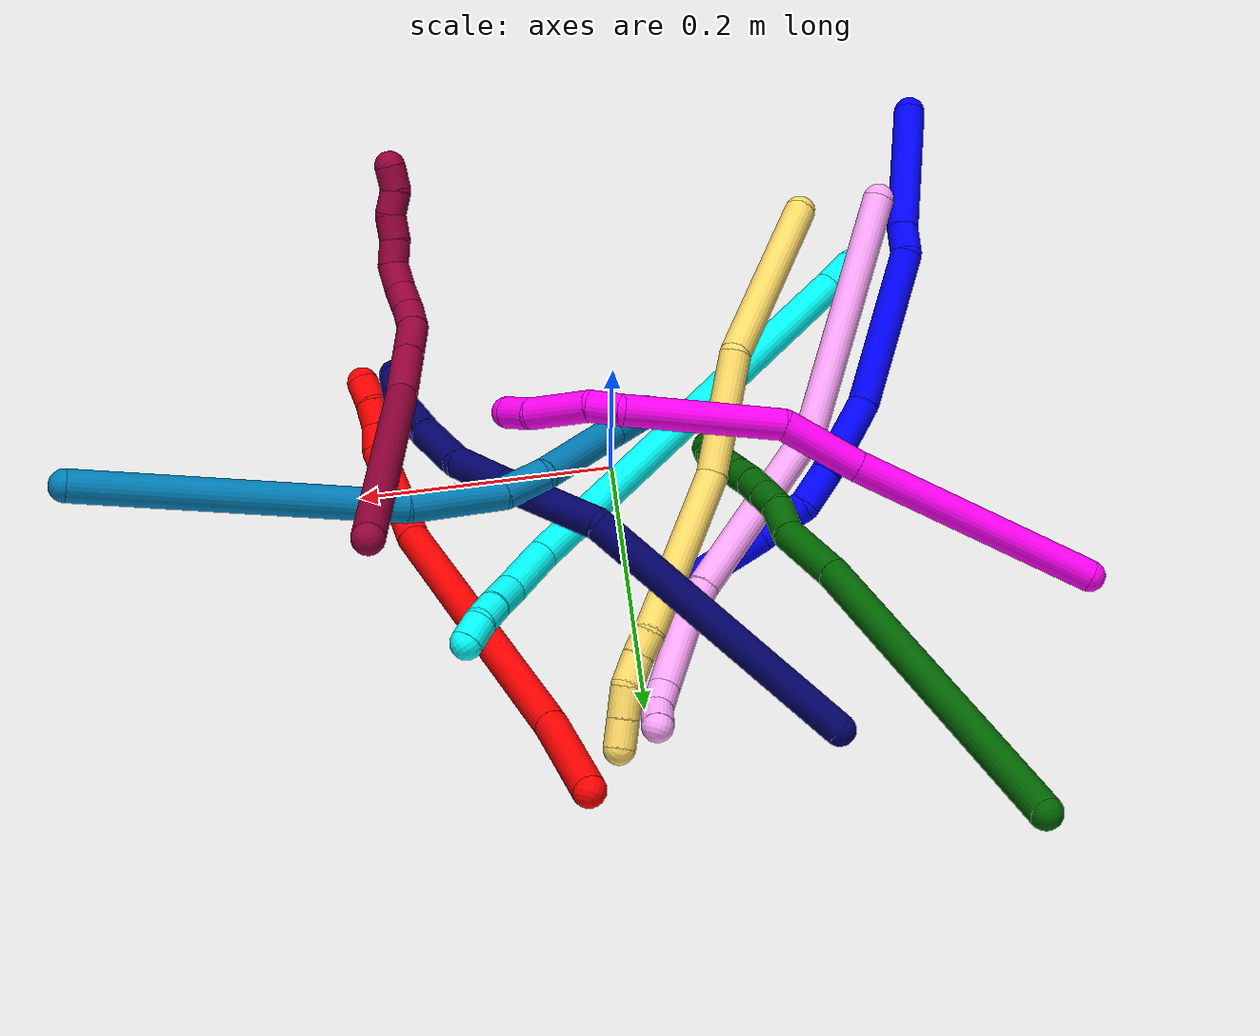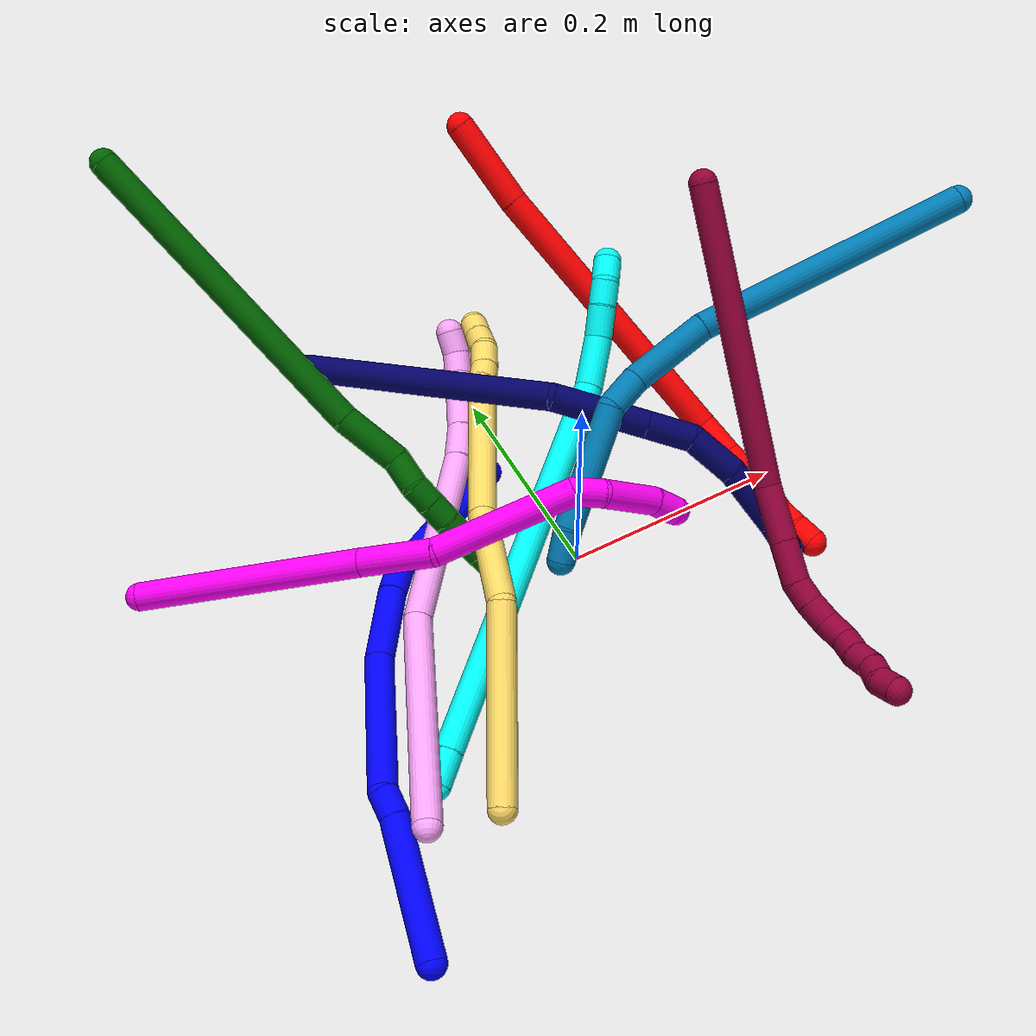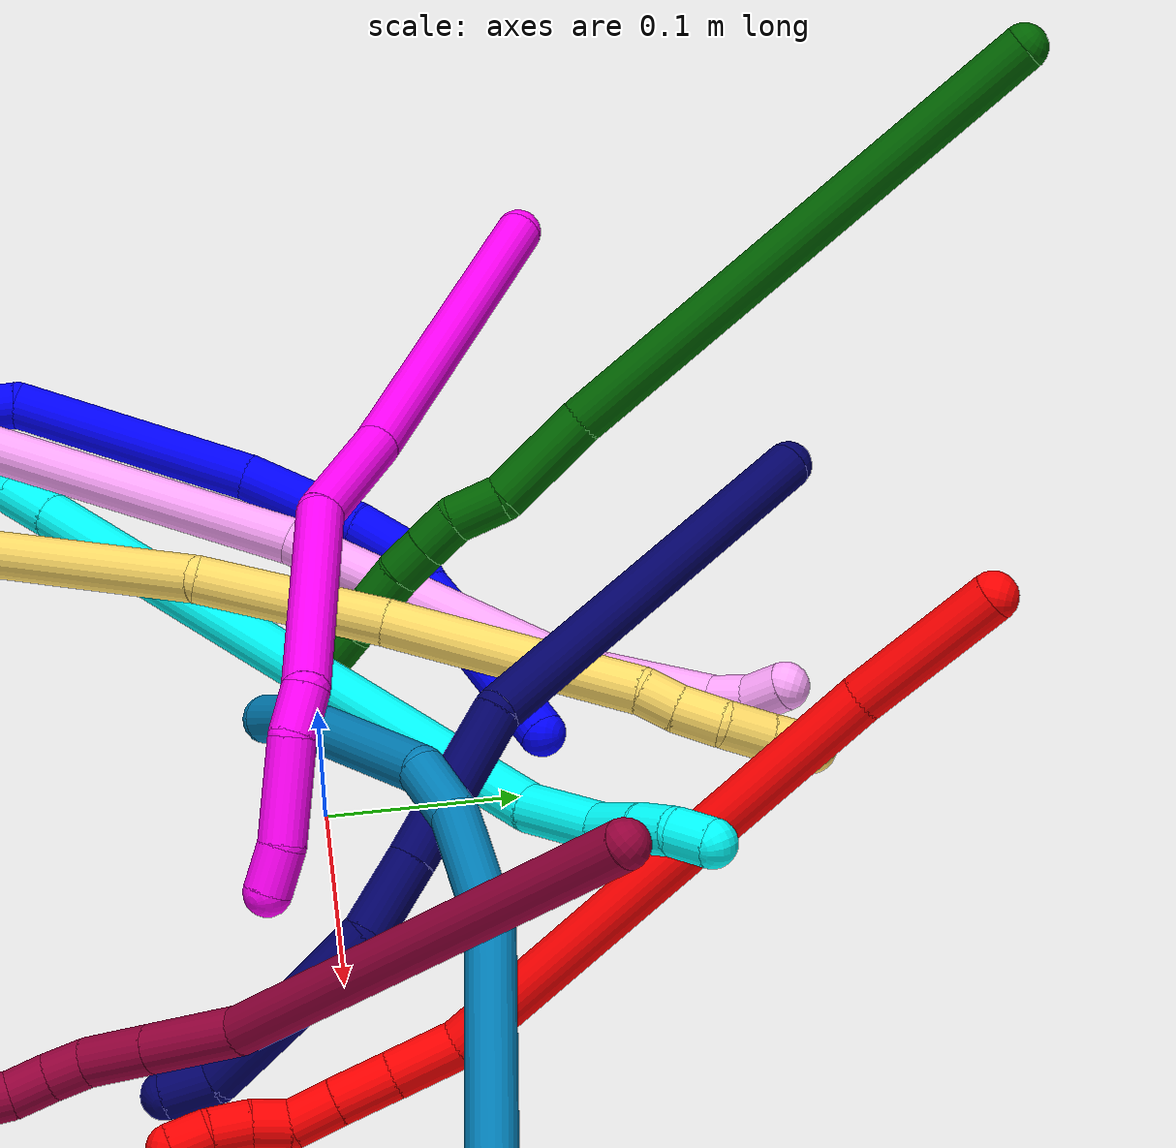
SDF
<sdf version="1.7">
 <world name="default">
  <plugin name="TubeGeneratorPlugin" filename="libtube_generator_plugin.so"/>
  <model name="photoneo_s_sensor">
   <static>1</static>
   <pose>0 0 2 1.57079 1.57079 3.14159</pose>
   <link name="link">
    <inertial><mass>0.1</mass></inertial>
    <sensor name="sensor" type="depth">
     <update_rate>30</update_rate>
     <camera>
      <horizontal_fov>1.22</horizontal_fov>
      <image><width>1920</width><height>1200</height><format>B8G8R8</format></image>
      <clip><near>0.1</near><far>2</far></clip>
      <depth_camera><output>points</output></depth_camera>
     </camera>
     <plugin name="camera_plugin" filename="libgazebo_ros_depth_camera.so">
      <baseline>0.2</baseline>
      <alwaysOn>1</alwaysOn>
      <updateRate>0.0</updateRate>
      <cameraName>camera_ir</cameraName>
      <imageTopicName>/camera/color/image_raw</imageTopicName>
      <cameraInfoTopicName>/camera/color/camera_info</cameraInfoTopicName>
      <depthImageTopicName>/camera/depth/image_raw</depthImageTopicName>
      <depthImageCameraInfoTopicName>/camera/depth/camera_info</depthImageCameraInfoTopicName>
      <pointCloudTopicName>/camera/depth/points</pointCloudTopicName>
      <frameName>fr_optical</frameName>
      <pointCloudCutoff>0.1</pointCloudCutoff>
      <pointCloudCutoffMax>2.0</pointCloudCutoffMax>
      <distortionK1>0</distortionK1>
      <distortionK2>0</distortionK2>
      <distortionK3>0</distortionK3>
      <distortionT1>0</distortionT1>
      <distortionT2>0</distortionT2>
      <CxPrime>0</CxPrime>
      <Cx>0</Cx>
      <Cy>0</Cy>
      <focalLength>0</focalLength>
      <hackBaseline>0</hackBaseline>
     </plugin>
    </sensor>
   </link>
  </model>
  <gravity>0 0 -9.8</gravity>
  <magnetic_field>6e-06 2.3e-05 -4.2e-05</magnetic_field>
  <atmosphere type="adiabatic"/>
  <physics name="default_physics" default="0" type="ode">
   <max_step_size>0.003</max_step_size>
   <real_time_factor>1</real_time_factor>
   <real_time_update_rate>1000</real_time_update_rate>
   <max_contacts>10000</max_contacts>
   <ode>
    <solver>
     <type>quick</type>
     <iters>100</iters>
     <sor>1.3</sor>
     <use_dynamic_moi_rescaling>0</use_dynamic_moi_rescaling>
    </solver>
    <constraints>
     <contact_max_correcting_vel>0</contact_max_correcting_vel>
     <contact_surface_layer>0.001</contact_surface_layer>
     <cfm>0</cfm>
     <erp>0.2</erp>
    </constraints>
   </ode>
  </physics>
  <scene><ambient>0.4 0.4 0.4 1</ambient><background>0.7 0.7 0.7 1</background><shadows>0</shadows></scene>
  <audio><device>default</device></audio>
  <spherical_coordinates>
   <surface_model>EARTH_WGS84</surface_model>
   <latitude_deg>0</latitude_deg>
   <longitude_deg>0</longitude_deg>
   <elevation>0</elevation>
   <heading_deg>0</heading_deg>
  </spherical_coordinates>
  <model name="bin">
   <static>1</static>
   <link name="bottom">
    <collision name="collision-bottom">
     <pose>0 0 -0.01 0 -0 0</pose>
     <geometry><box><size>0.8 0.6 0.02</size></box></geometry>
     <surface>
      <friction><ode><mu>100</mu><mu2>100</mu2></ode></friction>
      <contact><collide_bitmask>65535</collide_bitmask></contact>
     </surface>
    </collision>
   </link>
   <link name="west_wall">
    <collision name="collision-west_wall">
     <pose>-0.41 0 0.1 0 -0 0</pose>
     <geometry><box><size>0.02 0.6 0.2</size></box></geometry>
     <surface>
      <friction><ode><mu>100</mu><mu2>100</mu2></ode></friction>
      <contact><collide_bitmask>65535</collide_bitmask></contact>
     </surface>
    </collision>
   </link>
   <link name="east_wall">
    <collision name="collision-east_wall">
     <pose>0.41 0 0.1 0 -0 0</pose>
     <geometry><box><size>0.02 0.6 0.2</size></box></geometry>
     <surface>
      <friction><ode><mu>100</mu><mu2>100</mu2></ode></friction>
      <contact><collide_bitmask>65535</collide_bitmask></contact>
     </surface>
    </collision>
   </link>
   <link name="south_wall">
    <collision name="collision-south_wall">
     <pose>0 -0.31 0.1 0 -0 0</pose>
     <geometry><box><size>0.8 0.02 0.2</size></box></geometry>
     <surface>
      <friction><ode><mu>100</mu><mu2>100</mu2></ode></friction>
      <contact><collide_bitmask>65535</collide_bitmask></contact>
     </surface>
    </collision>
   </link>
   <link name="north_wall">
    <collision name="collision-north_wall">
     <pose>0 0.31 0.1 0 -0 0</pose>
     <geometry><box><size>0.8 0.02 0.2</size></box></geometry>
     <surface>
      <friction><ode><mu>100</mu><mu2>100</mu2></ode></friction>
      <contact><collide_bitmask>65535</collide_bitmask></contact>
     </surface>
    </collision>
   </link>
  </model>
  <model name="1">
   <static>0</static>
   <link name="1">
    <collision name="collision-cylinder-e_1_1_4">
     <pose>0.012238 -0.013355 -0.055549 2.90565 0.211017 1.45844</pose>
     <geometry><cylinder><radius>0.0125</radius><length>0.116855</length></cylinder></geometry>
     <surface>
      <friction><ode><mu>1.16</mu><mu2>1.16</mu2><slip1>0</slip1><slip2>0</slip2></ode></friction>
      <contact><ode><kp>1e+06</kp><kd>1</kd><max_vel>0</max_vel><min_depth>0.001</min_depth></ode></contact>
     </surface>
    </collision>
    <visual name="visual-cylinder-e_1_1_4">
     <pose>0.012238 -0.013355 -0.055549 2.90565 0.211017 1.45844</pose>
     <geometry><cylinder><radius>0.0125</radius><length>0.116855</length></cylinder></geometry>
     <material><ambient>0 0 1 1</ambient></material>
    </visual>
    <collision name="collision-cylinder-e_2_4_5">
     <pose>0.026934 -0.031324 -0.121598 2.72765 0.211114 0.934603</pose>
     <geometry><cylinder><radius>0.0125</radius><length>0.02346</length></cylinder></geometry>
     <surface>
      <friction><ode><mu>1.16</mu><mu2>1.16</mu2><slip1>0</slip1><slip2>0</slip2></ode></friction>
      <contact><ode><kp>1e+06</kp><kd>1</kd><max_vel>0</max_vel><min_depth>0.001</min_depth></ode></contact>
     </surface>
    </collision>
    <visual name="visual-cylinder-e_2_4_5">
     <pose>0.026934 -0.031324 -0.121598 2.72765 0.211114 0.934603</pose>
     <geometry><cylinder><radius>0.0125</radius><length>0.02346</length></cylinder></geometry>
     <material><ambient>0 0 1 1</ambient></material>
    </visual>
    <collision name="collision-cylinder-e_3_5_6">
     <pose>0.059278 -0.038342 -0.189851 3.09998 0.47719 2.97088</pose>
     <geometry><cylinder><radius>0.0125</radius><length>0.130142</length></cylinder></geometry>
     <surface>
      <friction><ode><mu>1.16</mu><mu2>1.16</mu2><slip1>0</slip1><slip2>0</slip2></ode></friction>
      <contact><ode><kp>1e+06</kp><kd>1</kd><max_vel>0</max_vel><min_depth>0.001</min_depth></ode></contact>
     </surface>
    </collision>
    <visual name="visual-cylinder-e_3_5_6">
     <pose>0.059278 -0.038342 -0.189851 3.09998 0.47719 2.97088</pose>
     <geometry><cylinder><radius>0.0125</radius><length>0.130142</length></cylinder></geometry>
     <material><ambient>0 0 1 1</ambient></material>
    </visual>
    <collision name="collision-cylinder-e_4_6_7">
     <pose>0.100899 -0.035458 -0.278739 -2.97333 0.355753 -2.26439</pose>
     <geometry><cylinder><radius>0.0125</radius><length>0.067384</length></cylinder></geometry>
     <surface>
      <friction><ode><mu>1.16</mu><mu2>1.16</mu2><slip1>0</slip1><slip2>0</slip2></ode></friction>
      <contact><ode><kp>1e+06</kp><kd>1</kd><max_vel>0</max_vel><min_depth>0.001</min_depth></ode></contact>
     </surface>
    </collision>
    <visual name="visual-cylinder-e_4_6_7">
     <pose>0.100899 -0.035458 -0.278739 -2.97333 0.355753 -2.26439</pose>
     <geometry><cylinder><radius>0.0125</radius><length>0.067384</length></cylinder></geometry>
     <material><ambient>0 0 1 1</ambient></material>
    </visual>
    <collision name="collision-cylinder-e_5_7_8">
     <pose>0.118834 -0.026183 -0.323952 -2.86568 0.400862 -1.9426</pose>
     <geometry><cylinder><radius>0.0125</radius><length>0.031781</length></cylinder></geometry>
     <surface>
      <friction><ode><mu>1.16</mu><mu2>1.16</mu2><slip1>0</slip1><slip2>0</slip2></ode></friction>
      <contact><ode><kp>1e+06</kp><kd>1</kd><max_vel>0</max_vel><min_depth>0.001</min_depth></ode></contact>
     </surface>
    </collision>
    <visual name="visual-cylinder-e_5_7_8">
     <pose>0.118834 -0.026183 -0.323952 -2.86568 0.400862 -1.9426</pose>
     <geometry><cylinder><radius>0.0125</radius><length>0.031781</length></cylinder></geometry>
     <material><ambient>0 0 1 1</ambient></material>
    </visual>
    <collision name="collision-cylinder-e_6_8_9">
     <pose>0.129754 -0.015557 -0.344317 -2.32888 0.476451 -1.02757</pose>
     <geometry><cylinder><radius>0.0125</radius><length>0.020582</length></cylinder></geometry>
     <surface>
      <friction><ode><mu>1.16</mu><mu2>1.16</mu2><slip1>0</slip1><slip2>0</slip2></ode></friction>
      <contact><ode><kp>1e+06</kp><kd>1</kd><max_vel>0</max_vel><min_depth>0.001</min_depth></ode></contact>
     </surface>
    </collision>
    <visual name="visual-cylinder-e_6_8_9">
     <pose>0.129754 -0.015557 -0.344317 -2.32888 0.476451 -1.02757</pose>
     <geometry><cylinder><radius>0.0125</radius><length>0.020582</length></cylinder></geometry>
     <material><ambient>0 0 1 1</ambient></material>
    </visual>
    <collision name="collision-cylinder-e_7_9_10">
     <pose>0.139019 -0.002932 -0.358589 -2.49847 0.427456 -1.15492</pose>
     <geometry><cylinder><radius>0.0125</radius><length>0.021929</length></cylinder></geometry>
     <surface>
      <friction><ode><mu>1.16</mu><mu2>1.16</mu2><slip1>0</slip1><slip2>0</slip2></ode></friction>
      <contact><ode><kp>1e+06</kp><kd>1</kd><max_vel>0</max_vel><min_depth>0.001</min_depth></ode></contact>
     </surface>
    </collision>
    <visual name="visual-cylinder-e_7_9_10">
     <pose>0.139019 -0.002932 -0.358589 -2.49847 0.427456 -1.15492</pose>
     <geometry><cylinder><radius>0.0125</radius><length>0.021929</length></cylinder></geometry>
     <material><ambient>0 0 1 1</ambient></material>
    </visual>
    <collision name="collision-cylinder-e_8_10_2">
     <pose>0.155215 0.02981 -0.399413 -2.45787 0.268383 -0.725247</pose>
     <geometry><cylinder><radius>0.0125</radius><length>0.087868</length></cylinder></geometry>
     <surface>
      <friction><ode><mu>1.16</mu><mu2>1.16</mu2><slip1>0</slip1><slip2>0</slip2></ode></friction>
      <contact><ode><kp>1e+06</kp><kd>1</kd><max_vel>0</max_vel><min_depth>0.001</min_depth></ode></contact>
     </surface>
    </collision>
    <visual name="visual-cylinder-e_8_10_2">
     <pose>0.155215 0.02981 -0.399413 -2.45787 0.268383 -0.725247</pose>
     <geometry><cylinder><radius>0.0125</radius><length>0.087868</length></cylinder></geometry>
     <material><ambient>0 0 1 1</ambient></material>
    </visual>
    <collision name="collision-sphere-2">
     <pose>0.166865 0.056569 -0.432252 0 -0 0</pose>
     <geometry><sphere><radius>0.0125</radius></sphere></geometry>
     <surface>
      <friction><ode><mu>1.16</mu><mu2>1.16</mu2><slip1>0</slip1><slip2>0</slip2></ode></friction>
      <contact><ode><kp>1e+06</kp><kd>1</kd><max_vel>0</max_vel><min_depth>0.001</min_depth></ode></contact>
     </surface>
    </collision>
    <visual name="visual-sphere-2">
     <pose>0.166865 0.056569 -0.432252 0 -0 0</pose>
     <geometry><sphere><radius>0.0125</radius></sphere></geometry>
     <material><ambient>0 0 1 1</ambient></material>
    </visual>
    <collision name="collision-sphere-10">
     <pose>0.143565 0.003051 -0.366573 0 -0 0</pose>
     <geometry><sphere><radius>0.0125</radius></sphere></geometry>
     <surface>
      <friction><ode><mu>1.16</mu><mu2>1.16</mu2><slip1>0</slip1><slip2>0</slip2></ode></friction>
      <contact><ode><kp>1e+06</kp><kd>1</kd><max_vel>0</max_vel><min_depth>0.001</min_depth></ode></contact>
     </surface>
    </collision>
    <visual name="visual-sphere-10">
     <pose>0.143565 0.003051 -0.366573 0 -0 0</pose>
     <geometry><sphere><radius>0.0125</radius></sphere></geometry>
     <material><ambient>0 0 1 1</ambient></material>
    </visual>
    <collision name="collision-sphere-9">
     <pose>0.134474 -0.008916 -0.350604 0 -0 0</pose>
     <geometry><sphere><radius>0.0125</radius></sphere></geometry>
     <surface>
      <friction><ode><mu>1.16</mu><mu2>1.16</mu2><slip1>0</slip1><slip2>0</slip2></ode></friction>
      <contact><ode><kp>1e+06</kp><kd>1</kd><max_vel>0</max_vel><min_depth>0.001</min_depth></ode></contact>
     </surface>
    </collision>
    <visual name="visual-sphere-9">
     <pose>0.134474 -0.008916 -0.350604 0 -0 0</pose>
     <geometry><sphere><radius>0.0125</radius></sphere></geometry>
     <material><ambient>0 0 1 1</ambient></material>
    </visual>
    <collision name="collision-sphere-4">
     <pose>0.024476 -0.02671 -0.111097 0 -0 0</pose>
     <geometry><sphere><radius>0.0125</radius></sphere></geometry>
     <surface>
      <friction><ode><mu>1.16</mu><mu2>1.16</mu2><slip1>0</slip1><slip2>0</slip2></ode></friction>
      <contact><ode><kp>1e+06</kp><kd>1</kd><max_vel>0</max_vel><min_depth>0.001</min_depth></ode></contact>
     </surface>
    </collision>
    <visual name="visual-sphere-4">
     <pose>0.024476 -0.02671 -0.111097 0 -0 0</pose>
     <geometry><sphere><radius>0.0125</radius></sphere></geometry>
     <material><ambient>0 0 1 1</ambient></material>
    </visual>
    <collision name="collision-sphere-1">
     <geometry><sphere><radius>0.0125</radius></sphere></geometry>
     <surface>
      <friction><ode><mu>1.16</mu><mu2>1.16</mu2><slip1>0</slip1><slip2>0</slip2></ode></friction>
      <contact><ode><kp>1e+06</kp><kd>1</kd><max_vel>0</max_vel><min_depth>0.001</min_depth></ode></contact>
     </surface>
    </collision>
    <visual name="visual-sphere-1">
     <geometry><sphere><radius>0.0125</radius></sphere></geometry>
     <material><ambient>0 0 1 1</ambient></material>
    </visual>
    <collision name="collision-sphere-8">
     <pose>0.125035 -0.022197 -0.338029 0 -0 0</pose>
     <geometry><sphere><radius>0.0125</radius></sphere></geometry>
     <surface>
      <friction><ode><mu>1.16</mu><mu2>1.16</mu2><slip1>0</slip1><slip2>0</slip2></ode></friction>
      <contact><ode><kp>1e+06</kp><kd>1</kd><max_vel>0</max_vel><min_depth>0.001</min_depth></ode></contact>
     </surface>
    </collision>
    <visual name="visual-sphere-8">
     <pose>0.125035 -0.022197 -0.338029 0 -0 0</pose>
     <geometry><sphere><radius>0.0125</radius></sphere></geometry>
     <material><ambient>0 0 1 1</ambient></material>
    </visual>
    <collision name="collision-sphere-5">
     <pose>0.029392 -0.035937 -0.132099 0 -0 0</pose>
     <geometry><sphere><radius>0.0125</radius></sphere></geometry>
     <surface>
      <friction><ode><mu>1.16</mu><mu2>1.16</mu2><slip1>0</slip1><slip2>0</slip2></ode></friction>
      <contact><ode><kp>1e+06</kp><kd>1</kd><max_vel>0</max_vel><min_depth>0.001</min_depth></ode></contact>
     </surface>
    </collision>
    <visual name="visual-sphere-5">
     <pose>0.029392 -0.035937 -0.132099 0 -0 0</pose>
     <geometry><sphere><radius>0.0125</radius></sphere></geometry>
     <material><ambient>0 0 1 1</ambient></material>
    </visual>
    <collision name="collision-sphere-6">
     <pose>0.089164 -0.040746 -0.247602 0 -0 0</pose>
     <geometry><sphere><radius>0.0125</radius></sphere></geometry>
     <surface>
      <friction><ode><mu>1.16</mu><mu2>1.16</mu2><slip1>0</slip1><slip2>0</slip2></ode></friction>
      <contact><ode><kp>1e+06</kp><kd>1</kd><max_vel>0</max_vel><min_depth>0.001</min_depth></ode></contact>
     </surface>
    </collision>
    <visual name="visual-sphere-6">
     <pose>0.089164 -0.040746 -0.247602 0 -0 0</pose>
     <geometry><sphere><radius>0.0125</radius></sphere></geometry>
     <material><ambient>0 0 1 1</ambient></material>
    </visual>
    <collision name="collision-sphere-7">
     <pose>0.112633 -0.030169 -0.309875 0 -0 0</pose>
     <geometry><sphere><radius>0.0125</radius></sphere></geometry>
     <surface>
      <friction><ode><mu>1.16</mu><mu2>1.16</mu2><slip1>0</slip1><slip2>0</slip2></ode></friction>
      <contact><ode><kp>1e+06</kp><kd>1</kd><max_vel>0</max_vel><min_depth>0.001</min_depth></ode></contact>
     </surface>
    </collision>
    <visual name="visual-sphere-7">
     <pose>0.112633 -0.030169 -0.309875 0 -0 0</pose>
     <geometry><sphere><radius>0.0125</radius></sphere></geometry>
     <material><ambient>0 0 1 1</ambient></material>
    </visual>
    <inertial>
     <pose>0.079419 -0.016544 -0.22635 0 -0 0</pose>
     <mass>0.5</mass>
     <inertia>
      <ixx>-1e-05</ixx>
      <ixy>0</ixy>
      <ixz>0</ixz>
      <iyy>0.000273</iyy>
      <iyz>0</iyz>
      <izz>-0.000183</izz>
     </inertia>
    </inertial>
   </link>
   <pose>-0.283018 -0.276353 0.011498 -3.11821 1.19737 1.13836</pose>
  </model>
  <model name="2">
   <static>0</static>
   <link name="2">
    <collision name="collision-cylinder-e_1_1_4">
     <pose>0.01417 -0.028217 -0.025943 2.31424 0.35409 0.773995</pose>
     <geometry><cylinder><radius>0.0125</radius><length>0.081732</length></cylinder></geometry>
     <surface>
      <friction><ode><mu>1.16</mu><mu2>1.16</mu2><slip1>0</slip1><slip2>0</slip2></ode></friction>
      <contact><ode><kp>1e+06</kp><kd>1</kd><max_vel>0</max_vel><min_depth>0.001</min_depth></ode></contact>
     </surface>
    </collision>
    <visual name="visual-cylinder-e_1_1_4">
     <pose>0.01417 -0.028217 -0.025943 2.31424 0.35409 0.773995</pose>
     <geometry><cylinder><radius>0.0125</radius><length>0.081732</length></cylinder></geometry>
     <material><ambient>1 0 0 1</ambient></material>
    </visual>
    <collision name="collision-cylinder-e_2_4_5">
     <pose>0.067219 -0.155731 -0.130804 2.24234 0.297435 0.602039</pose>
     <geometry><cylinder><radius>0.0125</radius><length>0.265327</length></cylinder></geometry>
     <surface>
      <friction><ode><mu>1.16</mu><mu2>1.16</mu2><slip1>0</slip1><slip2>0</slip2></ode></friction>
      <contact><ode><kp>1e+06</kp><kd>1</kd><max_vel>0</max_vel><min_depth>0.001</min_depth></ode></contact>
     </surface>
    </collision>
    <visual name="visual-cylinder-e_2_4_5">
     <pose>0.067219 -0.155731 -0.130804 2.24234 0.297435 0.602039</pose>
     <geometry><cylinder><radius>0.0125</radius><length>0.265327</length></cylinder></geometry>
     <material><ambient>1 0 0 1</ambient></material>
    </visual>
    <collision name="collision-cylinder-e_3_5_6">
     <pose>0.107432 -0.266294 -0.223483 2.45554 0.074827 0.208848</pose>
     <geometry><cylinder><radius>0.0125</radius><length>0.035669</length></cylinder></geometry>
     <surface>
      <friction><ode><mu>1.16</mu><mu2>1.16</mu2><slip1>0</slip1><slip2>0</slip2></ode></friction>
      <contact><ode><kp>1e+06</kp><kd>1</kd><max_vel>0</max_vel><min_depth>0.001</min_depth></ode></contact>
     </surface>
    </collision>
    <visual name="visual-cylinder-e_3_5_6">
     <pose>0.107432 -0.266294 -0.223483 2.45554 0.074827 0.208848</pose>
     <geometry><cylinder><radius>0.0125</radius><length>0.035669</length></cylinder></geometry>
     <material><ambient>1 0 0 1</ambient></material>
    </visual>
    <collision name="collision-cylinder-e_4_6_7">
     <pose>0.109196 -0.287541 -0.249219 2.44678 0.027641 0.076305</pose>
     <geometry><cylinder><radius>0.0125</radius><length>0.03119</length></cylinder></geometry>
     <surface>
      <friction><ode><mu>1.16</mu><mu2>1.16</mu2><slip1>0</slip1><slip2>0</slip2></ode></friction>
      <contact><ode><kp>1e+06</kp><kd>1</kd><max_vel>0</max_vel><min_depth>0.001</min_depth></ode></contact>
     </surface>
    </collision>
    <visual name="visual-cylinder-e_4_6_7">
     <pose>0.109196 -0.287541 -0.249219 2.44678 0.027641 0.076305</pose>
     <geometry><cylinder><radius>0.0125</radius><length>0.03119</length></cylinder></geometry>
     <material><ambient>1 0 0 1</ambient></material>
    </visual>
    <collision name="collision-cylinder-e_5_7_8">
     <pose>0.110061 -0.305705 -0.270591 2.42513 0.034813 0.092931</pose>
     <geometry><cylinder><radius>0.0125</radius><length>0.024936</length></cylinder></geometry>
     <surface>
      <friction><ode><mu>1.16</mu><mu2>1.16</mu2><slip1>0</slip1><slip2>0</slip2></ode></friction>
      <contact><ode><kp>1e+06</kp><kd>1</kd><max_vel>0</max_vel><min_depth>0.001</min_depth></ode></contact>
     </surface>
    </collision>
    <visual name="visual-cylinder-e_5_7_8">
     <pose>0.110061 -0.305705 -0.270591 2.42513 0.034813 0.092931</pose>
     <geometry><cylinder><radius>0.0125</radius><length>0.024936</length></cylinder></geometry>
     <material><ambient>1 0 0 1</ambient></material>
    </visual>
    <collision name="collision-cylinder-e_6_8_9">
     <pose>0.108275 -0.316691 -0.289392 2.85187 -0.222468 -1.30689</pose>
     <geometry><cylinder><radius>0.0125</radius><length>0.020122</length></cylinder></geometry>
     <surface>
      <friction><ode><mu>1.16</mu><mu2>1.16</mu2><slip1>0</slip1><slip2>0</slip2></ode></friction>
      <contact><ode><kp>1e+06</kp><kd>1</kd><max_vel>0</max_vel><min_depth>0.001</min_depth></ode></contact>
     </surface>
    </collision>
    <visual name="visual-cylinder-e_6_8_9">
     <pose>0.108275 -0.316691 -0.289392 2.85187 -0.222468 -1.30689</pose>
     <geometry><cylinder><radius>0.0125</radius><length>0.020122</length></cylinder></geometry>
     <material><ambient>1 0 0 1</ambient></material>
    </visual>
    <collision name="collision-cylinder-e_7_9_10">
     <pose>0.103282 -0.324377 -0.307482 2.6295 -0.271485 -0.961738</pose>
     <geometry><cylinder><radius>0.0125</radius><length>0.020685</length></cylinder></geometry>
     <surface>
      <friction><ode><mu>1.16</mu><mu2>1.16</mu2><slip1>0</slip1><slip2>0</slip2></ode></friction>
      <contact><ode><kp>1e+06</kp><kd>1</kd><max_vel>0</max_vel><min_depth>0.001</min_depth></ode></contact>
     </surface>
    </collision>
    <visual name="visual-cylinder-e_7_9_10">
     <pose>0.103282 -0.324377 -0.307482 2.6295 -0.271485 -0.961738</pose>
     <geometry><cylinder><radius>0.0125</radius><length>0.020685</length></cylinder></geometry>
     <material><ambient>1 0 0 1</ambient></material>
    </visual>
    <collision name="collision-cylinder-e_8_10_2">
     <pose>0.09935 -0.335589 -0.324043 2.4646 -0.114084 -0.321612</pose>
     <geometry><cylinder><radius>0.0125</radius><length>0.02034</length></cylinder></geometry>
     <surface>
      <friction><ode><mu>1.16</mu><mu2>1.16</mu2><slip1>0</slip1><slip2>0</slip2></ode></friction>
      <contact><ode><kp>1e+06</kp><kd>1</kd><max_vel>0</max_vel><min_depth>0.001</min_depth></ode></contact>
     </surface>
    </collision>
    <visual name="visual-cylinder-e_8_10_2">
     <pose>0.09935 -0.335589 -0.324043 2.4646 -0.114084 -0.321612</pose>
     <geometry><cylinder><radius>0.0125</radius><length>0.02034</length></cylinder></geometry>
     <material><ambient>1 0 0 1</ambient></material>
    </visual>
    <collision name="collision-sphere-2">
     <pose>0.098193 -0.341918 -0.331918 0 -0 0</pose>
     <geometry><sphere><radius>0.0125</radius></sphere></geometry>
     <surface>
      <friction><ode><mu>1.16</mu><mu2>1.16</mu2><slip1>0</slip1><slip2>0</slip2></ode></friction>
      <contact><ode><kp>1e+06</kp><kd>1</kd><max_vel>0</max_vel><min_depth>0.001</min_depth></ode></contact>
     </surface>
    </collision>
    <visual name="visual-sphere-2">
     <pose>0.098193 -0.341918 -0.331918 0 -0 0</pose>
     <geometry><sphere><radius>0.0125</radius></sphere></geometry>
     <material><ambient>1 0 0 1</ambient></material>
    </visual>
    <collision name="collision-sphere-10">
     <pose>0.100508 -0.329259 -0.316167 0 -0 0</pose>
     <geometry><sphere><radius>0.0125</radius></sphere></geometry>
     <surface>
      <friction><ode><mu>1.16</mu><mu2>1.16</mu2><slip1>0</slip1><slip2>0</slip2></ode></friction>
      <contact><ode><kp>1e+06</kp><kd>1</kd><max_vel>0</max_vel><min_depth>0.001</min_depth></ode></contact>
     </surface>
    </collision>
    <visual name="visual-sphere-10">
     <pose>0.100508 -0.329259 -0.316167 0 -0 0</pose>
     <geometry><sphere><radius>0.0125</radius></sphere></geometry>
     <material><ambient>1 0 0 1</ambient></material>
    </visual>
    <collision name="collision-sphere-9">
     <pose>0.106055 -0.319495 -0.298796 0 -0 0</pose>
     <geometry><sphere><radius>0.0125</radius></sphere></geometry>
     <surface>
      <friction><ode><mu>1.16</mu><mu2>1.16</mu2><slip1>0</slip1><slip2>0</slip2></ode></friction>
      <contact><ode><kp>1e+06</kp><kd>1</kd><max_vel>0</max_vel><min_depth>0.001</min_depth></ode></contact>
     </surface>
    </collision>
    <visual name="visual-sphere-9">
     <pose>0.106055 -0.319495 -0.298796 0 -0 0</pose>
     <geometry><sphere><radius>0.0125</radius></sphere></geometry>
     <material><ambient>1 0 0 1</ambient></material>
    </visual>
    <collision name="collision-sphere-4">
     <pose>0.028339 -0.056434 -0.051886 0 -0 0</pose>
     <geometry><sphere><radius>0.0125</radius></sphere></geometry>
     <surface>
      <friction><ode><mu>1.16</mu><mu2>1.16</mu2><slip1>0</slip1><slip2>0</slip2></ode></friction>
      <contact><ode><kp>1e+06</kp><kd>1</kd><max_vel>0</max_vel><min_depth>0.001</min_depth></ode></contact>
     </surface>
    </collision>
    <visual name="visual-sphere-4">
     <pose>0.028339 -0.056434 -0.051886 0 -0 0</pose>
     <geometry><sphere><radius>0.0125</radius></sphere></geometry>
     <material><ambient>1 0 0 1</ambient></material>
    </visual>
    <collision name="collision-sphere-1">
     <geometry><sphere><radius>0.0125</radius></sphere></geometry>
     <surface>
      <friction><ode><mu>1.16</mu><mu2>1.16</mu2><slip1>0</slip1><slip2>0</slip2></ode></friction>
      <contact><ode><kp>1e+06</kp><kd>1</kd><max_vel>0</max_vel><min_depth>0.001</min_depth></ode></contact>
     </surface>
    </collision>
    <visual name="visual-sphere-1">
     <geometry><sphere><radius>0.0125</radius></sphere></geometry>
     <material><ambient>1 0 0 1</ambient></material>
    </visual>
    <collision name="collision-sphere-8">
     <pose>0.110495 -0.313888 -0.279988 0 -0 0</pose>
     <geometry><sphere><radius>0.0125</radius></sphere></geometry>
     <surface>
      <friction><ode><mu>1.16</mu><mu2>1.16</mu2><slip1>0</slip1><slip2>0</slip2></ode></friction>
      <contact><ode><kp>1e+06</kp><kd>1</kd><max_vel>0</max_vel><min_depth>0.001</min_depth></ode></contact>
     </surface>
    </collision>
    <visual name="visual-sphere-8">
     <pose>0.110495 -0.313888 -0.279988 0 -0 0</pose>
     <geometry><sphere><radius>0.0125</radius></sphere></geometry>
     <material><ambient>1 0 0 1</ambient></material>
    </visual>
    <collision name="collision-sphere-5">
     <pose>0.106098 -0.255028 -0.209722 0 -0 0</pose>
     <geometry><sphere><radius>0.0125</radius></sphere></geometry>
     <surface>
      <friction><ode><mu>1.16</mu><mu2>1.16</mu2><slip1>0</slip1><slip2>0</slip2></ode></friction>
      <contact><ode><kp>1e+06</kp><kd>1</kd><max_vel>0</max_vel><min_depth>0.001</min_depth></ode></contact>
     </surface>
    </collision>
    <visual name="visual-sphere-5">
     <pose>0.106098 -0.255028 -0.209722 0 -0 0</pose>
     <geometry><sphere><radius>0.0125</radius></sphere></geometry>
     <material><ambient>1 0 0 1</ambient></material>
    </visual>
    <collision name="collision-sphere-6">
     <pose>0.108765 -0.27756 -0.237244 0 -0 0</pose>
     <geometry><sphere><radius>0.0125</radius></sphere></geometry>
     <surface>
      <friction><ode><mu>1.16</mu><mu2>1.16</mu2><slip1>0</slip1><slip2>0</slip2></ode></friction>
      <contact><ode><kp>1e+06</kp><kd>1</kd><max_vel>0</max_vel><min_depth>0.001</min_depth></ode></contact>
     </surface>
    </collision>
    <visual name="visual-sphere-6">
     <pose>0.108765 -0.27756 -0.237244 0 -0 0</pose>
     <geometry><sphere><radius>0.0125</radius></sphere></geometry>
     <material><ambient>1 0 0 1</ambient></material>
    </visual>
    <collision name="collision-sphere-7">
     <pose>0.109627 -0.297522 -0.261194 0 -0 0</pose>
     <geometry><sphere><radius>0.0125</radius></sphere></geometry>
     <surface>
      <friction><ode><mu>1.16</mu><mu2>1.16</mu2><slip1>0</slip1><slip2>0</slip2></ode></friction>
      <contact><ode><kp>1e+06</kp><kd>1</kd><max_vel>0</max_vel><min_depth>0.001</min_depth></ode></contact>
     </surface>
    </collision>
    <visual name="visual-sphere-7">
     <pose>0.109627 -0.297522 -0.261194 0 -0 0</pose>
     <geometry><sphere><radius>0.0125</radius></sphere></geometry>
     <material><ambient>1 0 0 1</ambient></material>
    </visual>
    <inertial>
     <pose>0.070622 -0.179247 -0.156185 0 -0 0</pose>
     <mass>0.5</mass>
     <inertia>
      <ixx>0.002168</ixx>
      <ixy>0</ixy>
      <ixz>0</ixz>
      <iyy>0.000227</iyy>
      <iyz>0</iyz>
      <izz>0.000714</izz>
     </inertia>
    </inertial>
   </link>
   <pose>0.058066 0.321662 0.230423 1.44646 1.23314 2.5952</pose>
  </model>
  <model name="3">
   <static>0</static>
   <link name="3">
    <collision name="collision-cylinder-e_1_1_4">
     <pose>0.011645 0.00959 0.001448 -1.42089 0.876336 -0.766334</pose>
     <geometry><cylinder><radius>0.0125</radius><length>0.030309</length></cylinder></geometry>
     <surface>
      <friction><ode><mu>1.16</mu><mu2>1.16</mu2><slip1>0</slip1><slip2>0</slip2></ode></friction>
      <contact><ode><kp>1e+06</kp><kd>1</kd><max_vel>0</max_vel><min_depth>0.001</min_depth></ode></contact>
     </surface>
    </collision>
    <visual name="visual-cylinder-e_1_1_4">
     <pose>0.011645 0.00959 0.001448 -1.42089 0.876336 -0.766334</pose>
     <geometry><cylinder><radius>0.0125</radius><length>0.030309</length></cylinder></geometry>
     <material><ambient>0.003922 1 0.996078 1</ambient></material>
    </visual>
    <collision name="collision-cylinder-e_2_4_5">
     <pose>0.158544 0.130022 0.016573 -1.44804 0.880561 -0.789415</pose>
     <geometry><cylinder><radius>0.0125</radius><length>0.35081</length></cylinder></geometry>
     <surface>
      <friction><ode><mu>1.16</mu><mu2>1.16</mu2><slip1>0</slip1><slip2>0</slip2></ode></friction>
      <contact><ode><kp>1e+06</kp><kd>1</kd><max_vel>0</max_vel><min_depth>0.001</min_depth></ode></contact>
     </surface>
    </collision>
    <visual name="visual-cylinder-e_2_4_5">
     <pose>0.158544 0.130022 0.016573 -1.44804 0.880561 -0.789415</pose>
     <geometry><cylinder><radius>0.0125</radius><length>0.35081</length></cylinder></geometry>
     <material><ambient>0.003922 1 0.996078 1</ambient></material>
    </visual>
    <collision name="collision-cylinder-e_3_5_6">
     <pose>0.3152 0.250438 0.032529 -1.33688 1.13986 -0.937035</pose>
     <geometry><cylinder><radius>0.0125</radius><length>0.047113</length></cylinder></geometry>
     <surface>
      <friction><ode><mu>1.16</mu><mu2>1.16</mu2><slip1>0</slip1><slip2>0</slip2></ode></friction>
      <contact><ode><kp>1e+06</kp><kd>1</kd><max_vel>0</max_vel><min_depth>0.001</min_depth></ode></contact>
     </surface>
    </collision>
    <visual name="visual-cylinder-e_3_5_6">
     <pose>0.3152 0.250438 0.032529 -1.33688 1.13986 -0.937035</pose>
     <geometry><cylinder><radius>0.0125</radius><length>0.047113</length></cylinder></geometry>
     <material><ambient>0.003922 1 0.996078 1</ambient></material>
    </visual>
    <collision name="collision-cylinder-e_4_6_7">
     <pose>0.350658 0.262679 0.035259 -1.40438 1.38051 -1.21961</pose>
     <geometry><cylinder><radius>0.0125</radius><length>0.028625</length></cylinder></geometry>
     <surface>
      <friction><ode><mu>1.16</mu><mu2>1.16</mu2><slip1>0</slip1><slip2>0</slip2></ode></friction>
      <contact><ode><kp>1e+06</kp><kd>1</kd><max_vel>0</max_vel><min_depth>0.001</min_depth></ode></contact>
     </surface>
    </collision>
    <visual name="visual-cylinder-e_4_6_7">
     <pose>0.350658 0.262679 0.035259 -1.40438 1.38051 -1.21961</pose>
     <geometry><cylinder><radius>0.0125</radius><length>0.028625</length></cylinder></geometry>
     <material><ambient>0.003922 1 0.996078 1</ambient></material>
    </visual>
    <collision name="collision-cylinder-e_5_7_8">
     <pose>0.375276 0.268495 0.036685 -1.26947 1.26848 -0.992909</pose>
     <geometry><cylinder><radius>0.0125</radius><length>0.022131</length></cylinder></geometry>
     <surface>
      <friction><ode><mu>1.16</mu><mu2>1.16</mu2><slip1>0</slip1><slip2>0</slip2></ode></friction>
      <contact><ode><kp>1e+06</kp><kd>1</kd><max_vel>0</max_vel><min_depth>0.001</min_depth></ode></contact>
     </surface>
    </collision>
    <visual name="visual-cylinder-e_5_7_8">
     <pose>0.375276 0.268495 0.036685 -1.26947 1.26848 -0.992909</pose>
     <geometry><cylinder><radius>0.0125</radius><length>0.022131</length></cylinder></geometry>
     <material><ambient>0.003922 1 0.996078 1</ambient></material>
    </visual>
    <collision name="collision-cylinder-e_6_8_2">
     <pose>0.394402 0.276995 0.04056 -1.07482 0.952763 -0.596652</pose>
     <geometry><cylinder><radius>0.0125</radius><length>0.021011</length></cylinder></geometry>
     <surface>
      <friction><ode><mu>1.16</mu><mu2>1.16</mu2><slip1>0</slip1><slip2>0</slip2></ode></friction>
      <contact><ode><kp>1e+06</kp><kd>1</kd><max_vel>0</max_vel><min_depth>0.001</min_depth></ode></contact>
     </surface>
    </collision>
    <visual name="visual-cylinder-e_6_8_2">
     <pose>0.394402 0.276995 0.04056 -1.07482 0.952763 -0.596652</pose>
     <geometry><cylinder><radius>0.0125</radius><length>0.021011</length></cylinder></geometry>
     <material><ambient>0.003922 1 0.996078 1</ambient></material>
    </visual>
    <collision name="collision-sphere-2">
     <pose>0.402964 0.282349 0.043457 0 -0 0</pose>
     <geometry><sphere><radius>0.0125</radius></sphere></geometry>
     <surface>
      <friction><ode><mu>1.16</mu><mu2>1.16</mu2><slip1>0</slip1><slip2>0</slip2></ode></friction>
      <contact><ode><kp>1e+06</kp><kd>1</kd><max_vel>0</max_vel><min_depth>0.001</min_depth></ode></contact>
     </surface>
    </collision>
    <visual name="visual-sphere-2">
     <pose>0.402964 0.282349 0.043457 0 -0 0</pose>
     <geometry><sphere><radius>0.0125</radius></sphere></geometry>
     <material><ambient>0.003922 1 0.996078 1</ambient></material>
    </visual>
    <collision name="collision-sphere-4">
     <pose>0.023289 0.019179 0.002897 0 -0 0</pose>
     <geometry><sphere><radius>0.0125</radius></sphere></geometry>
     <surface>
      <friction><ode><mu>1.16</mu><mu2>1.16</mu2><slip1>0</slip1><slip2>0</slip2></ode></friction>
      <contact><ode><kp>1e+06</kp><kd>1</kd><max_vel>0</max_vel><min_depth>0.001</min_depth></ode></contact>
     </surface>
    </collision>
    <visual name="visual-sphere-4">
     <pose>0.023289 0.019179 0.002897 0 -0 0</pose>
     <geometry><sphere><radius>0.0125</radius></sphere></geometry>
     <material><ambient>0.003922 1 0.996078 1</ambient></material>
    </visual>
    <collision name="collision-sphere-1">
     <geometry><sphere><radius>0.0125</radius></sphere></geometry>
     <surface>
      <friction><ode><mu>1.16</mu><mu2>1.16</mu2><slip1>0</slip1><slip2>0</slip2></ode></friction>
      <contact><ode><kp>1e+06</kp><kd>1</kd><max_vel>0</max_vel><min_depth>0.001</min_depth></ode></contact>
     </surface>
    </collision>
    <visual name="visual-sphere-1">
     <geometry><sphere><radius>0.0125</radius></sphere></geometry>
     <material><ambient>0.003922 1 0.996078 1</ambient></material>
    </visual>
    <collision name="collision-sphere-8">
     <pose>0.38584 0.271642 0.037663 0 -0 0</pose>
     <geometry><sphere><radius>0.0125</radius></sphere></geometry>
     <surface>
      <friction><ode><mu>1.16</mu><mu2>1.16</mu2><slip1>0</slip1><slip2>0</slip2></ode></friction>
      <contact><ode><kp>1e+06</kp><kd>1</kd><max_vel>0</max_vel><min_depth>0.001</min_depth></ode></contact>
     </surface>
    </collision>
    <visual name="visual-sphere-8">
     <pose>0.38584 0.271642 0.037663 0 -0 0</pose>
     <geometry><sphere><radius>0.0125</radius></sphere></geometry>
     <material><ambient>0.003922 1 0.996078 1</ambient></material>
    </visual>
    <collision name="collision-sphere-5">
     <pose>0.293798 0.240866 0.030248 0 -0 0</pose>
     <geometry><sphere><radius>0.0125</radius></sphere></geometry>
     <surface>
      <friction><ode><mu>1.16</mu><mu2>1.16</mu2><slip1>0</slip1><slip2>0</slip2></ode></friction>
      <contact><ode><kp>1e+06</kp><kd>1</kd><max_vel>0</max_vel><min_depth>0.001</min_depth></ode></contact>
     </surface>
    </collision>
    <visual name="visual-sphere-5">
     <pose>0.293798 0.240866 0.030248 0 -0 0</pose>
     <geometry><sphere><radius>0.0125</radius></sphere></geometry>
     <material><ambient>0.003922 1 0.996078 1</ambient></material>
    </visual>
    <collision name="collision-sphere-6">
     <pose>0.336603 0.26001 0.03481 0 -0 0</pose>
     <geometry><sphere><radius>0.0125</radius></sphere></geometry>
     <surface>
      <friction><ode><mu>1.16</mu><mu2>1.16</mu2><slip1>0</slip1><slip2>0</slip2></ode></friction>
      <contact><ode><kp>1e+06</kp><kd>1</kd><max_vel>0</max_vel><min_depth>0.001</min_depth></ode></contact>
     </surface>
    </collision>
    <visual name="visual-sphere-6">
     <pose>0.336603 0.26001 0.03481 0 -0 0</pose>
     <geometry><sphere><radius>0.0125</radius></sphere></geometry>
     <material><ambient>0.003922 1 0.996078 1</ambient></material>
    </visual>
    <collision name="collision-sphere-7">
     <pose>0.364712 0.265349 0.035707 0 -0 0</pose>
     <geometry><sphere><radius>0.0125</radius></sphere></geometry>
     <surface>
      <friction><ode><mu>1.16</mu><mu2>1.16</mu2><slip1>0</slip1><slip2>0</slip2></ode></friction>
      <contact><ode><kp>1e+06</kp><kd>1</kd><max_vel>0</max_vel><min_depth>0.001</min_depth></ode></contact>
     </surface>
    </collision>
    <visual name="visual-sphere-7">
     <pose>0.364712 0.265349 0.035707 0 -0 0</pose>
     <geometry><sphere><radius>0.0125</radius></sphere></geometry>
     <material><ambient>0.003922 1 0.996078 1</ambient></material>
    </visual>
    <inertial>
     <pose>0.194903 0.153968 0.020127 0 -0 0</pose>
     <mass>0.5</mass>
     <inertia>
      <ixx>1.7e-05</ixx>
      <ixy>0</ixy>
      <ixz>0</ixz>
      <iyy>0.000674</iyy>
      <iyz>0</iyz>
      <izz>-0.00509</izz>
     </inertia>
    </inertial>
   </link>
   <pose>-0.214043 -0.146354 0.011493 -2.15163 -0.86842 1.01089</pose>
  </model>
  <model name="4">
   <static>0</static>
   <link name="4">
    <collision name="collision-cylinder-e_1_1_4">
     <pose>0.000107 -5.3e-05 0.101879 0.000516 0.001049 0</pose>
     <geometry><cylinder><radius>0.0125</radius><length>0.203758</length></cylinder></geometry>
     <surface>
      <friction><ode><mu>1.16</mu><mu2>1.16</mu2><slip1>0</slip1><slip2>0</slip2></ode></friction>
      <contact><ode><kp>1e+06</kp><kd>1</kd><max_vel>0</max_vel><min_depth>0.001</min_depth></ode></contact>
     </surface>
    </collision>
    <visual name="visual-cylinder-e_1_1_4">
     <pose>0.000107 -5.3e-05 0.101879 0.000516 0.001049 0</pose>
     <geometry><cylinder><radius>0.0125</radius><length>0.203758</length></cylinder></geometry>
     <material><ambient>1 0.65098 0.996078 1</ambient></material>
    </visual>
    <collision name="collision-cylinder-e_2_4_5">
     <pose>-0.025573 0.011509 0.279934 -0.151299 -0.322929 0.02469</pose>
     <geometry><cylinder><radius>0.0125</radius><length>0.162515</length></cylinder></geometry>
     <surface>
      <friction><ode><mu>1.16</mu><mu2>1.16</mu2><slip1>0</slip1><slip2>0</slip2></ode></friction>
      <contact><ode><kp>1e+06</kp><kd>1</kd><max_vel>0</max_vel><min_depth>0.001</min_depth></ode></contact>
     </surface>
    </collision>
    <visual name="visual-cylinder-e_2_4_5">
     <pose>-0.025573 0.011509 0.279934 -0.151299 -0.322929 0.02469</pose>
     <geometry><cylinder><radius>0.0125</radius><length>0.162515</length></cylinder></geometry>
     <material><ambient>1 0.65098 0.996078 1</ambient></material>
    </visual>
    <collision name="collision-cylinder-e_3_5_6">
     <pose>-0.054468 0.02584 0.371539 -0.174282 -0.195871 0.017166</pose>
     <geometry><cylinder><radius>0.0125</radius><length>0.031942</length></cylinder></geometry>
     <surface>
      <friction><ode><mu>1.16</mu><mu2>1.16</mu2><slip1>0</slip1><slip2>0</slip2></ode></friction>
      <contact><ode><kp>1e+06</kp><kd>1</kd><max_vel>0</max_vel><min_depth>0.001</min_depth></ode></contact>
     </surface>
    </collision>
    <visual name="visual-cylinder-e_3_5_6">
     <pose>-0.054468 0.02584 0.371539 -0.174282 -0.195871 0.017166</pose>
     <geometry><cylinder><radius>0.0125</radius><length>0.031942</length></cylinder></geometry>
     <material><ambient>1 0.65098 0.996078 1</ambient></material>
    </visual>
    <collision name="collision-cylinder-e_4_6_7">
     <pose>-0.059524 0.034026 0.415941 -0.186589 -0.06597 0.006175</pose>
     <geometry><cylinder><radius>0.0125</radius><length>0.059099</length></cylinder></geometry>
     <surface>
      <friction><ode><mu>1.16</mu><mu2>1.16</mu2><slip1>0</slip1><slip2>0</slip2></ode></friction>
      <contact><ode><kp>1e+06</kp><kd>1</kd><max_vel>0</max_vel><min_depth>0.001</min_depth></ode></contact>
     </surface>
    </collision>
    <visual name="visual-cylinder-e_4_6_7">
     <pose>-0.059524 0.034026 0.415941 -0.186589 -0.06597 0.006175</pose>
     <geometry><cylinder><radius>0.0125</radius><length>0.059099</length></cylinder></geometry>
     <material><ambient>1 0.65098 0.996078 1</ambient></material>
    </visual>
    <collision name="collision-cylinder-e_5_7_8">
     <pose>-0.062624 0.044574 0.454369 -0.492894 -0.106948 0.026928</pose>
     <geometry><cylinder><radius>0.0125</radius><length>0.021586</length></cylinder></geometry>
     <surface>
      <friction><ode><mu>1.16</mu><mu2>1.16</mu2><slip1>0</slip1><slip2>0</slip2></ode></friction>
      <contact><ode><kp>1e+06</kp><kd>1</kd><max_vel>0</max_vel><min_depth>0.001</min_depth></ode></contact>
     </surface>
    </collision>
    <visual name="visual-cylinder-e_5_7_8">
     <pose>-0.062624 0.044574 0.454369 -0.492894 -0.106948 0.026928</pose>
     <geometry><cylinder><radius>0.0125</radius><length>0.021586</length></cylinder></geometry>
     <material><ambient>1 0.65098 0.996078 1</ambient></material>
    </visual>
    <collision name="collision-cylinder-e_6_8_2">
     <pose>-0.063136 0.057011 0.471355 -0.773775 0.060735 -0.024751</pose>
     <geometry><cylinder><radius>0.0125</radius><length>0.021101</length></cylinder></geometry>
     <surface>
      <friction><ode><mu>1.16</mu><mu2>1.16</mu2><slip1>0</slip1><slip2>0</slip2></ode></friction>
      <contact><ode><kp>1e+06</kp><kd>1</kd><max_vel>0</max_vel><min_depth>0.001</min_depth></ode></contact>
     </surface>
    </collision>
    <visual name="visual-cylinder-e_6_8_2">
     <pose>-0.063136 0.057011 0.471355 -0.773775 0.060735 -0.024751</pose>
     <geometry><cylinder><radius>0.0125</radius><length>0.021101</length></cylinder></geometry>
     <material><ambient>1 0.65098 0.996078 1</ambient></material>
    </visual>
    <collision name="collision-sphere-2">
     <pose>-0.062496 0.06437 0.478888 0 -0 0</pose>
     <geometry><sphere><radius>0.0125</radius></sphere></geometry>
     <surface>
      <friction><ode><mu>1.16</mu><mu2>1.16</mu2><slip1>0</slip1><slip2>0</slip2></ode></friction>
      <contact><ode><kp>1e+06</kp><kd>1</kd><max_vel>0</max_vel><min_depth>0.001</min_depth></ode></contact>
     </surface>
    </collision>
    <visual name="visual-sphere-2">
     <pose>-0.062496 0.06437 0.478888 0 -0 0</pose>
     <geometry><sphere><radius>0.0125</radius></sphere></geometry>
     <material><ambient>1 0.65098 0.996078 1</ambient></material>
    </visual>
    <collision name="collision-sphere-4">
     <pose>0.000214 -0.000105 0.203757 0 -0 0</pose>
     <geometry><sphere><radius>0.0125</radius></sphere></geometry>
     <surface>
      <friction><ode><mu>1.16</mu><mu2>1.16</mu2><slip1>0</slip1><slip2>0</slip2></ode></friction>
      <contact><ode><kp>1e+06</kp><kd>1</kd><max_vel>0</max_vel><min_depth>0.001</min_depth></ode></contact>
     </surface>
    </collision>
    <visual name="visual-sphere-4">
     <pose>0.000214 -0.000105 0.203757 0 -0 0</pose>
     <geometry><sphere><radius>0.0125</radius></sphere></geometry>
     <material><ambient>1 0.65098 0.996078 1</ambient></material>
    </visual>
    <collision name="collision-sphere-1">
     <geometry><sphere><radius>0.0125</radius></sphere></geometry>
     <surface>
      <friction><ode><mu>1.16</mu><mu2>1.16</mu2><slip1>0</slip1><slip2>0</slip2></ode></friction>
      <contact><ode><kp>1e+06</kp><kd>1</kd><max_vel>0</max_vel><min_depth>0.001</min_depth></ode></contact>
     </surface>
    </collision>
    <visual name="visual-sphere-1">
     <geometry><sphere><radius>0.0125</radius></sphere></geometry>
     <material><ambient>1 0.65098 0.996078 1</ambient></material>
    </visual>
    <collision name="collision-sphere-8">
     <pose>-0.063776 0.049651 0.463823 0 -0 0</pose>
     <geometry><sphere><radius>0.0125</radius></sphere></geometry>
     <surface>
      <friction><ode><mu>1.16</mu><mu2>1.16</mu2><slip1>0</slip1><slip2>0</slip2></ode></friction>
      <contact><ode><kp>1e+06</kp><kd>1</kd><max_vel>0</max_vel><min_depth>0.001</min_depth></ode></contact>
     </surface>
    </collision>
    <visual name="visual-sphere-8">
     <pose>-0.063776 0.049651 0.463823 0 -0 0</pose>
     <geometry><sphere><radius>0.0125</radius></sphere></geometry>
     <material><ambient>1 0.65098 0.996078 1</ambient></material>
    </visual>
    <collision name="collision-sphere-5">
     <pose>-0.05136 0.023123 0.356111 0 -0 0</pose>
     <geometry><sphere><radius>0.0125</radius></sphere></geometry>
     <surface>
      <friction><ode><mu>1.16</mu><mu2>1.16</mu2><slip1>0</slip1><slip2>0</slip2></ode></friction>
      <contact><ode><kp>1e+06</kp><kd>1</kd><max_vel>0</max_vel><min_depth>0.001</min_depth></ode></contact>
     </surface>
    </collision>
    <visual name="visual-sphere-5">
     <pose>-0.05136 0.023123 0.356111 0 -0 0</pose>
     <geometry><sphere><radius>0.0125</radius></sphere></geometry>
     <material><ambient>1 0.65098 0.996078 1</ambient></material>
    </visual>
    <collision name="collision-sphere-6">
     <pose>-0.057576 0.028556 0.386968 0 -0 0</pose>
     <geometry><sphere><radius>0.0125</radius></sphere></geometry>
     <surface>
      <friction><ode><mu>1.16</mu><mu2>1.16</mu2><slip1>0</slip1><slip2>0</slip2></ode></friction>
      <contact><ode><kp>1e+06</kp><kd>1</kd><max_vel>0</max_vel><min_depth>0.001</min_depth></ode></contact>
     </surface>
    </collision>
    <visual name="visual-sphere-6">
     <pose>-0.057576 0.028556 0.386968 0 -0 0</pose>
     <geometry><sphere><radius>0.0125</radius></sphere></geometry>
     <material><ambient>1 0.65098 0.996078 1</ambient></material>
    </visual>
    <collision name="collision-sphere-7">
     <pose>-0.061472 0.039496 0.444915 0 -0 0</pose>
     <geometry><sphere><radius>0.0125</radius></sphere></geometry>
     <surface>
      <friction><ode><mu>1.16</mu><mu2>1.16</mu2><slip1>0</slip1><slip2>0</slip2></ode></friction>
      <contact><ode><kp>1e+06</kp><kd>1</kd><max_vel>0</max_vel><min_depth>0.001</min_depth></ode></contact>
     </surface>
    </collision>
    <visual name="visual-sphere-7">
     <pose>-0.061472 0.039496 0.444915 0 -0 0</pose>
     <geometry><sphere><radius>0.0125</radius></sphere></geometry>
     <material><ambient>1 0.65098 0.996078 1</ambient></material>
    </visual>
    <inertial>
     <pose>-0.024152 0.013722 0.244911 0 -0 0</pose>
     <mass>0.5</mass>
     <inertia>
      <ixx>0.001088</ixx>
      <ixy>0</ixy>
      <ixz>0</ixz>
      <iyy>0.001113</iyy>
      <iyz>0</iyz>
      <izz>9.6e-05</izz>
     </inertia>
    </inertial>
   </link>
   <pose>-0.240749 -0.187995 0.040464 1.6669 0.254583 2.74761</pose>
  </model>
  <model name="5">
   <static>0</static>
   <link name="5">
    <collision name="collision-cylinder-e_1_1_4">
     <pose>0.036623 0.071599 0.024315 -1.24341 0.451042 -0.325845</pose>
     <geometry><cylinder><radius>0.0125</radius><length>0.168034</length></cylinder></geometry>
     <surface>
      <friction><ode><mu>1.16</mu><mu2>1.16</mu2><slip1>0</slip1><slip2>0</slip2></ode></friction>
      <contact><ode><kp>1e+06</kp><kd>1</kd><max_vel>0</max_vel><min_depth>0.001</min_depth></ode></contact>
     </surface>
    </collision>
    <visual name="visual-cylinder-e_1_1_4">
     <pose>0.036623 0.071599 0.024315 -1.24341 0.451042 -0.325845</pose>
     <geometry><cylinder><radius>0.0125</radius><length>0.168034</length></cylinder></geometry>
     <material><ambient>1 0.858824 0.4 1</ambient></material>
    </visual>
    <collision name="collision-cylinder-e_2_4_5">
     <pose>0.084888 0.191488 0.043478 -1.6771 0.235265 -0.261418</pose>
     <geometry><cylinder><radius>0.0125</radius><length>0.09988</length></cylinder></geometry>
     <surface>
      <friction><ode><mu>1.16</mu><mu2>1.16</mu2><slip1>0</slip1><slip2>0</slip2></ode></friction>
      <contact><ode><kp>1e+06</kp><kd>1</kd><max_vel>0</max_vel><min_depth>0.001</min_depth></ode></contact>
     </surface>
    </collision>
    <visual name="visual-cylinder-e_2_4_5">
     <pose>0.084888 0.191488 0.043478 -1.6771 0.235265 -0.261418</pose>
     <geometry><cylinder><radius>0.0125</radius><length>0.09988</length></cylinder></geometry>
     <material><ambient>1 0.858824 0.4 1</ambient></material>
    </visual>
    <collision name="collision-cylinder-e_3_5_6">
     <pose>0.125658 0.30341 0.042674 -1.50255 0.428418 -0.400912</pose>
     <geometry><cylinder><radius>0.0125</radius><length>0.140236</length></cylinder></geometry>
     <surface>
      <friction><ode><mu>1.16</mu><mu2>1.16</mu2><slip1>0</slip1><slip2>0</slip2></ode></friction>
      <contact><ode><kp>1e+06</kp><kd>1</kd><max_vel>0</max_vel><min_depth>0.001</min_depth></ode></contact>
     </surface>
    </collision>
    <visual name="visual-cylinder-e_3_5_6">
     <pose>0.125658 0.30341 0.042674 -1.50255 0.428418 -0.400912</pose>
     <geometry><cylinder><radius>0.0125</radius><length>0.140236</length></cylinder></geometry>
     <material><ambient>1 0.858824 0.4 1</ambient></material>
    </visual>
    <collision name="collision-cylinder-e_4_6_7">
     <pose>0.159384 0.375808 0.045198 -1.77619 0.474337 -0.577894</pose>
     <geometry><cylinder><radius>0.0125</radius><length>0.020129</length></cylinder></geometry>
     <surface>
      <friction><ode><mu>1.16</mu><mu2>1.16</mu2><slip1>0</slip1><slip2>0</slip2></ode></friction>
      <contact><ode><kp>1e+06</kp><kd>1</kd><max_vel>0</max_vel><min_depth>0.001</min_depth></ode></contact>
     </surface>
    </collision>
    <visual name="visual-cylinder-e_4_6_7">
     <pose>0.159384 0.375808 0.045198 -1.77619 0.474337 -0.577894</pose>
     <geometry><cylinder><radius>0.0125</radius><length>0.020129</length></cylinder></geometry>
     <material><ambient>1 0.858824 0.4 1</ambient></material>
    </visual>
    <collision name="collision-cylinder-e_5_7_8">
     <pose>0.168726 0.395805 0.04262 -1.63764 0.398876 -0.425672</pose>
     <geometry><cylinder><radius>0.0125</radius><length>0.024432</length></cylinder></geometry>
     <surface>
      <friction><ode><mu>1.16</mu><mu2>1.16</mu2><slip1>0</slip1><slip2>0</slip2></ode></friction>
      <contact><ode><kp>1e+06</kp><kd>1</kd><max_vel>0</max_vel><min_depth>0.001</min_depth></ode></contact>
     </surface>
    </collision>
    <visual name="visual-cylinder-e_5_7_8">
     <pose>0.168726 0.395805 0.04262 -1.63764 0.398876 -0.425672</pose>
     <geometry><cylinder><radius>0.0125</radius><length>0.024432</length></cylinder></geometry>
     <material><ambient>1 0.858824 0.4 1</ambient></material>
    </visual>
    <collision name="collision-cylinder-e_6_8_9">
     <pose>0.175095 0.418748 0.038152 -1.87804 0.131475 -0.179428</pose>
     <geometry><cylinder><radius>0.0125</radius><length>0.024787</length></cylinder></geometry>
     <surface>
      <friction><ode><mu>1.16</mu><mu2>1.16</mu2><slip1>0</slip1><slip2>0</slip2></ode></friction>
      <contact><ode><kp>1e+06</kp><kd>1</kd><max_vel>0</max_vel><min_depth>0.001</min_depth></ode></contact>
     </surface>
    </collision>
    <visual name="visual-cylinder-e_6_8_9">
     <pose>0.175095 0.418748 0.038152 -1.87804 0.131475 -0.179428</pose>
     <geometry><cylinder><radius>0.0125</radius><length>0.024787</length></cylinder></geometry>
     <material><ambient>1 0.858824 0.4 1</ambient></material>
    </visual>
    <collision name="collision-cylinder-e_7_9_2">
     <pose>0.178341 0.441228 0.031611 -1.8273 0.144636 -0.187242</pose>
     <geometry><cylinder><radius>0.0125</radius><length>0.022502</length></cylinder></geometry>
     <surface>
      <friction><ode><mu>1.16</mu><mu2>1.16</mu2><slip1>0</slip1><slip2>0</slip2></ode></friction>
      <contact><ode><kp>1e+06</kp><kd>1</kd><max_vel>0</max_vel><min_depth>0.001</min_depth></ode></contact>
     </surface>
    </collision>
    <visual name="visual-cylinder-e_7_9_2">
     <pose>0.178341 0.441228 0.031611 -1.8273 0.144636 -0.187242</pose>
     <geometry><cylinder><radius>0.0125</radius><length>0.022502</length></cylinder></geometry>
     <material><ambient>1 0.858824 0.4 1</ambient></material>
    </visual>
    <collision name="collision-sphere-2">
     <pose>0.179963 0.451998 0.028787 0 -0 0</pose>
     <geometry><sphere><radius>0.0125</radius></sphere></geometry>
     <surface>
      <friction><ode><mu>1.16</mu><mu2>1.16</mu2><slip1>0</slip1><slip2>0</slip2></ode></friction>
      <contact><ode><kp>1e+06</kp><kd>1</kd><max_vel>0</max_vel><min_depth>0.001</min_depth></ode></contact>
     </surface>
    </collision>
    <visual name="visual-sphere-2">
     <pose>0.179963 0.451998 0.028787 0 -0 0</pose>
     <geometry><sphere><radius>0.0125</radius></sphere></geometry>
     <material><ambient>1 0.858824 0.4 1</ambient></material>
    </visual>
    <collision name="collision-sphere-9">
     <pose>0.17672 0.430459 0.034436 0 -0 0</pose>
     <geometry><sphere><radius>0.0125</radius></sphere></geometry>
     <surface>
      <friction><ode><mu>1.16</mu><mu2>1.16</mu2><slip1>0</slip1><slip2>0</slip2></ode></friction>
      <contact><ode><kp>1e+06</kp><kd>1</kd><max_vel>0</max_vel><min_depth>0.001</min_depth></ode></contact>
     </surface>
    </collision>
    <visual name="visual-sphere-9">
     <pose>0.17672 0.430459 0.034436 0 -0 0</pose>
     <geometry><sphere><radius>0.0125</radius></sphere></geometry>
     <material><ambient>1 0.858824 0.4 1</ambient></material>
    </visual>
    <collision name="collision-sphere-4">
     <pose>0.073247 0.143198 0.04863 0 -0 0</pose>
     <geometry><sphere><radius>0.0125</radius></sphere></geometry>
     <surface>
      <friction><ode><mu>1.16</mu><mu2>1.16</mu2><slip1>0</slip1><slip2>0</slip2></ode></friction>
      <contact><ode><kp>1e+06</kp><kd>1</kd><max_vel>0</max_vel><min_depth>0.001</min_depth></ode></contact>
     </surface>
    </collision>
    <visual name="visual-sphere-4">
     <pose>0.073247 0.143198 0.04863 0 -0 0</pose>
     <geometry><sphere><radius>0.0125</radius></sphere></geometry>
     <material><ambient>1 0.858824 0.4 1</ambient></material>
    </visual>
    <collision name="collision-sphere-1">
     <geometry><sphere><radius>0.0125</radius></sphere></geometry>
     <surface>
      <friction><ode><mu>1.16</mu><mu2>1.16</mu2><slip1>0</slip1><slip2>0</slip2></ode></friction>
      <contact><ode><kp>1e+06</kp><kd>1</kd><max_vel>0</max_vel><min_depth>0.001</min_depth></ode></contact>
     </surface>
    </collision>
    <visual name="visual-sphere-1">
     <geometry><sphere><radius>0.0125</radius></sphere></geometry>
     <material><ambient>1 0.858824 0.4 1</ambient></material>
    </visual>
    <collision name="collision-sphere-8">
     <pose>0.17347 0.407036 0.041868 0 -0 0</pose>
     <geometry><sphere><radius>0.0125</radius></sphere></geometry>
     <surface>
      <friction><ode><mu>1.16</mu><mu2>1.16</mu2><slip1>0</slip1><slip2>0</slip2></ode></friction>
      <contact><ode><kp>1e+06</kp><kd>1</kd><max_vel>0</max_vel><min_depth>0.001</min_depth></ode></contact>
     </surface>
    </collision>
    <visual name="visual-sphere-8">
     <pose>0.17347 0.407036 0.041868 0 -0 0</pose>
     <geometry><sphere><radius>0.0125</radius></sphere></geometry>
     <material><ambient>1 0.858824 0.4 1</ambient></material>
    </visual>
    <collision name="collision-sphere-5">
     <pose>0.096529 0.239778 0.038325 0 -0 0</pose>
     <geometry><sphere><radius>0.0125</radius></sphere></geometry>
     <surface>
      <friction><ode><mu>1.16</mu><mu2>1.16</mu2><slip1>0</slip1><slip2>0</slip2></ode></friction>
      <contact><ode><kp>1e+06</kp><kd>1</kd><max_vel>0</max_vel><min_depth>0.001</min_depth></ode></contact>
     </surface>
    </collision>
    <visual name="visual-sphere-5">
     <pose>0.096529 0.239778 0.038325 0 -0 0</pose>
     <geometry><sphere><radius>0.0125</radius></sphere></geometry>
     <material><ambient>1 0.858824 0.4 1</ambient></material>
    </visual>
    <collision name="collision-sphere-6">
     <pose>0.154787 0.367043 0.047024 0 -0 0</pose>
     <geometry><sphere><radius>0.0125</radius></sphere></geometry>
     <surface>
      <friction><ode><mu>1.16</mu><mu2>1.16</mu2><slip1>0</slip1><slip2>0</slip2></ode></friction>
      <contact><ode><kp>1e+06</kp><kd>1</kd><max_vel>0</max_vel><min_depth>0.001</min_depth></ode></contact>
     </surface>
    </collision>
    <visual name="visual-sphere-6">
     <pose>0.154787 0.367043 0.047024 0 -0 0</pose>
     <geometry><sphere><radius>0.0125</radius></sphere></geometry>
     <material><ambient>1 0.858824 0.4 1</ambient></material>
    </visual>
    <collision name="collision-sphere-7">
     <pose>0.163981 0.384573 0.043372 0 -0 0</pose>
     <geometry><sphere><radius>0.0125</radius></sphere></geometry>
     <surface>
      <friction><ode><mu>1.16</mu><mu2>1.16</mu2><slip1>0</slip1><slip2>0</slip2></ode></friction>
      <contact><ode><kp>1e+06</kp><kd>1</kd><max_vel>0</max_vel><min_depth>0.001</min_depth></ode></contact>
     </surface>
    </collision>
    <visual name="visual-sphere-7">
     <pose>0.163981 0.384573 0.043372 0 -0 0</pose>
     <geometry><sphere><radius>0.0125</radius></sphere></geometry>
     <material><ambient>1 0.858824 0.4 1</ambient></material>
    </visual>
    <inertial>
     <pose>0.095876 0.222497 0.036042 0 -0 0</pose>
     <mass>0.5</mass>
     <inertia>
      <ixx>0.000419</ixx>
      <ixy>0</ixy>
      <ixz>0</ixz>
      <iyy>3.6e-05</iyy>
      <iyz>0</iyz>
      <izz>-0.00094</izz>
     </inertia>
    </inertial>
   </link>
   <pose>-0.178852 -0.194265 0.021093 -0.0379 -0.150519 -0.064577</pose>
  </model>
  <model name="6">
   <static>0</static>
   <link name="6">
    <collision name="collision-cylinder-e_1_1_4">
     <pose>0.010562 -0.035921 -0.142376 2.89445 0.071806 0.563021</pose>
     <geometry><cylinder><radius>0.0125</radius><length>0.294434</length></cylinder></geometry>
     <surface>
      <friction><ode><mu>1.16</mu><mu2>1.16</mu2><slip1>0</slip1><slip2>0</slip2></ode></friction>
      <contact><ode><kp>1e+06</kp><kd>1</kd><max_vel>0</max_vel><min_depth>0.001</min_depth></ode></contact>
     </surface>
    </collision>
    <visual name="visual-cylinder-e_1_1_4">
     <pose>0.010562 -0.035921 -0.142376 2.89445 0.071806 0.563021</pose>
     <geometry><cylinder><radius>0.0125</radius><length>0.294434</length></cylinder></geometry>
     <material><ambient>0 0.392157 0.003922 1</ambient></material>
    </visual>
    <collision name="collision-cylinder-e_2_4_5">
     <pose>0.027023 -0.079918 -0.311004 2.84315 0.211586 1.22993</pose>
     <geometry><cylinder><radius>0.0125</radius><length>0.056184</length></cylinder></geometry>
     <surface>
      <friction><ode><mu>1.16</mu><mu2>1.16</mu2><slip1>0</slip1><slip2>0</slip2></ode></friction>
      <contact><ode><kp>1e+06</kp><kd>1</kd><max_vel>0</max_vel><min_depth>0.001</min_depth></ode></contact>
     </surface>
    </collision>
    <visual name="visual-cylinder-e_2_4_5">
     <pose>0.027023 -0.079918 -0.311004 2.84315 0.211586 1.22993</pose>
     <geometry><cylinder><radius>0.0125</radius><length>0.056184</length></cylinder></geometry>
     <material><ambient>0 0.392157 0.003922 1</ambient></material>
    </visual>
    <collision name="collision-cylinder-e_3_5_6">
     <pose>0.030951 -0.093572 -0.349827 2.72401 -0.142391 -0.64936</pose>
     <geometry><cylinder><radius>0.0125</radius><length>0.027789</length></cylinder></geometry>
     <surface>
      <friction><ode><mu>1.16</mu><mu2>1.16</mu2><slip1>0</slip1><slip2>0</slip2></ode></friction>
      <contact><ode><kp>1e+06</kp><kd>1</kd><max_vel>0</max_vel><min_depth>0.001</min_depth></ode></contact>
     </surface>
    </collision>
    <visual name="visual-cylinder-e_3_5_6">
     <pose>0.030951 -0.093572 -0.349827 2.72401 -0.142391 -0.64936</pose>
     <geometry><cylinder><radius>0.0125</radius><length>0.027789</length></cylinder></geometry>
     <material><ambient>0 0.392157 0.003922 1</ambient></material>
    </visual>
    <collision name="collision-cylinder-e_4_6_7">
     <pose>0.029911 -0.101004 -0.372711 2.96363 0.088656 0.922795</pose>
     <geometry><cylinder><radius>0.0125</radius><length>0.021037</length></cylinder></geometry>
     <surface>
      <friction><ode><mu>1.16</mu><mu2>1.16</mu2><slip1>0</slip1><slip2>0</slip2></ode></friction>
      <contact><ode><kp>1e+06</kp><kd>1</kd><max_vel>0</max_vel><min_depth>0.001</min_depth></ode></contact>
     </surface>
    </collision>
    <visual name="visual-cylinder-e_4_6_7">
     <pose>0.029911 -0.101004 -0.372711 2.96363 0.088656 0.922795</pose>
     <geometry><cylinder><radius>0.0125</radius><length>0.021037</length></cylinder></geometry>
     <material><ambient>0 0.392157 0.003922 1</ambient></material>
    </visual>
    <collision name="collision-cylinder-e_5_7_8">
     <pose>0.031835 -0.104519 -0.393065 2.97778 0.097254 1.07027</pose>
     <geometry><cylinder><radius>0.0125</radius><length>0.020454</length></cylinder></geometry>
     <surface>
      <friction><ode><mu>1.16</mu><mu2>1.16</mu2><slip1>0</slip1><slip2>0</slip2></ode></friction>
      <contact><ode><kp>1e+06</kp><kd>1</kd><max_vel>0</max_vel><min_depth>0.001</min_depth></ode></contact>
     </surface>
    </collision>
    <visual name="visual-cylinder-e_5_7_8">
     <pose>0.031835 -0.104519 -0.393065 2.97778 0.097254 1.07027</pose>
     <geometry><cylinder><radius>0.0125</radius><length>0.020454</length></cylinder></geometry>
     <material><ambient>0 0.392157 0.003922 1</ambient></material>
    </visual>
    <collision name="collision-cylinder-e_6_8_9">
     <pose>0.034117 -0.1066 -0.413019 3.09912 0.129175 2.50696</pose>
     <geometry><cylinder><radius>0.0125</radius><length>0.020009</length></cylinder></geometry>
     <surface>
      <friction><ode><mu>1.16</mu><mu2>1.16</mu2><slip1>0</slip1><slip2>0</slip2></ode></friction>
      <contact><ode><kp>1e+06</kp><kd>1</kd><max_vel>0</max_vel><min_depth>0.001</min_depth></ode></contact>
     </surface>
    </collision>
    <visual name="visual-cylinder-e_6_8_9">
     <pose>0.034117 -0.1066 -0.413019 3.09912 0.129175 2.50696</pose>
     <geometry><cylinder><radius>0.0125</radius><length>0.020009</length></cylinder></geometry>
     <material><ambient>0 0.392157 0.003922 1</ambient></material>
    </visual>
    <collision name="collision-cylinder-e_7_9_10">
     <pose>0.037154 -0.108142 -0.432716 3.0275 0.175629 1.99073</pose>
     <geometry><cylinder><radius>0.0125</radius><length>0.020007</length></cylinder></geometry>
     <surface>
      <friction><ode><mu>1.16</mu><mu2>1.16</mu2><slip1>0</slip1><slip2>0</slip2></ode></friction>
      <contact><ode><kp>1e+06</kp><kd>1</kd><max_vel>0</max_vel><min_depth>0.001</min_depth></ode></contact>
     </surface>
    </collision>
    <visual name="visual-cylinder-e_7_9_10">
     <pose>0.037154 -0.108142 -0.432716 3.0275 0.175629 1.99073</pose>
     <geometry><cylinder><radius>0.0125</radius><length>0.020007</length></cylinder></geometry>
     <material><ambient>0 0.392157 0.003922 1</ambient></material>
    </visual>
    <collision name="collision-cylinder-e_8_10_11">
     <pose>0.040694 -0.110224 -0.452337 3.04429 0.179481 2.14966</pose>
     <geometry><cylinder><radius>0.0125</radius><length>0.020086</length></cylinder></geometry>
     <surface>
      <friction><ode><mu>1.16</mu><mu2>1.16</mu2><slip1>0</slip1><slip2>0</slip2></ode></friction>
      <contact><ode><kp>1e+06</kp><kd>1</kd><max_vel>0</max_vel><min_depth>0.001</min_depth></ode></contact>
     </surface>
    </collision>
    <visual name="visual-cylinder-e_8_10_11">
     <pose>0.040694 -0.110224 -0.452337 3.04429 0.179481 2.14966</pose>
     <geometry><cylinder><radius>0.0125</radius><length>0.020086</length></cylinder></geometry>
     <material><ambient>0 0.392157 0.003922 1</ambient></material>
    </visual>
    <collision name="collision-cylinder-e_9_11_2">
     <pose>0.04027 -0.109792 -0.471824 -2.99839 -0.223598 2.0046</pose>
     <geometry><cylinder><radius>0.0125</radius><length>0.020001</length></cylinder></geometry>
     <surface>
      <friction><ode><mu>1.16</mu><mu2>1.16</mu2><slip1>0</slip1><slip2>0</slip2></ode></friction>
      <contact><ode><kp>1e+06</kp><kd>1</kd><max_vel>0</max_vel><min_depth>0.001</min_depth></ode></contact>
     </surface>
    </collision>
    <visual name="visual-cylinder-e_9_11_2">
     <pose>0.04027 -0.109792 -0.471824 -2.99839 -0.223598 2.0046</pose>
     <geometry><cylinder><radius>0.0125</radius><length>0.020001</length></cylinder></geometry>
     <material><ambient>0 0.392157 0.003922 1</ambient></material>
    </visual>
    <collision name="collision-sphere-2">
     <pose>0.038052 -0.1084 -0.481475 0 -0 0</pose>
     <geometry><sphere><radius>0.0125</radius></sphere></geometry>
     <surface>
      <friction><ode><mu>1.16</mu><mu2>1.16</mu2><slip1>0</slip1><slip2>0</slip2></ode></friction>
      <contact><ode><kp>1e+06</kp><kd>1</kd><max_vel>0</max_vel><min_depth>0.001</min_depth></ode></contact>
     </surface>
    </collision>
    <visual name="visual-sphere-2">
     <pose>0.038052 -0.1084 -0.481475 0 -0 0</pose>
     <geometry><sphere><radius>0.0125</radius></sphere></geometry>
     <material><ambient>0 0.392157 0.003922 1</ambient></material>
    </visual>
    <collision name="collision-sphere-11">
     <pose>0.042487 -0.111184 -0.462172 0 -0 0</pose>
     <geometry><sphere><radius>0.0125</radius></sphere></geometry>
     <surface>
      <friction><ode><mu>1.16</mu><mu2>1.16</mu2><slip1>0</slip1><slip2>0</slip2></ode></friction>
      <contact><ode><kp>1e+06</kp><kd>1</kd><max_vel>0</max_vel><min_depth>0.001</min_depth></ode></contact>
     </surface>
    </collision>
    <visual name="visual-sphere-11">
     <pose>0.042487 -0.111184 -0.462172 0 -0 0</pose>
     <geometry><sphere><radius>0.0125</radius></sphere></geometry>
     <material><ambient>0 0.392157 0.003922 1</ambient></material>
    </visual>
    <collision name="collision-sphere-10">
     <pose>0.038901 -0.109264 -0.442502 0 -0 0</pose>
     <geometry><sphere><radius>0.0125</radius></sphere></geometry>
     <surface>
      <friction><ode><mu>1.16</mu><mu2>1.16</mu2><slip1>0</slip1><slip2>0</slip2></ode></friction>
      <contact><ode><kp>1e+06</kp><kd>1</kd><max_vel>0</max_vel><min_depth>0.001</min_depth></ode></contact>
     </surface>
    </collision>
    <visual name="visual-sphere-10">
     <pose>0.038901 -0.109264 -0.442502 0 -0 0</pose>
     <geometry><sphere><radius>0.0125</radius></sphere></geometry>
     <material><ambient>0 0.392157 0.003922 1</ambient></material>
    </visual>
    <collision name="collision-sphere-9">
     <pose>0.035406 -0.107021 -0.422931 0 -0 0</pose>
     <geometry><sphere><radius>0.0125</radius></sphere></geometry>
     <surface>
      <friction><ode><mu>1.16</mu><mu2>1.16</mu2><slip1>0</slip1><slip2>0</slip2></ode></friction>
      <contact><ode><kp>1e+06</kp><kd>1</kd><max_vel>0</max_vel><min_depth>0.001</min_depth></ode></contact>
     </surface>
    </collision>
    <visual name="visual-sphere-9">
     <pose>0.035406 -0.107021 -0.422931 0 -0 0</pose>
     <geometry><sphere><radius>0.0125</radius></sphere></geometry>
     <material><ambient>0 0.392157 0.003922 1</ambient></material>
    </visual>
    <collision name="collision-sphere-4">
     <pose>0.021124 -0.071842 -0.284752 0 -0 0</pose>
     <geometry><sphere><radius>0.0125</radius></sphere></geometry>
     <surface>
      <friction><ode><mu>1.16</mu><mu2>1.16</mu2><slip1>0</slip1><slip2>0</slip2></ode></friction>
      <contact><ode><kp>1e+06</kp><kd>1</kd><max_vel>0</max_vel><min_depth>0.001</min_depth></ode></contact>
     </surface>
    </collision>
    <visual name="visual-sphere-4">
     <pose>0.021124 -0.071842 -0.284752 0 -0 0</pose>
     <geometry><sphere><radius>0.0125</radius></sphere></geometry>
     <material><ambient>0 0.392157 0.003922 1</ambient></material>
    </visual>
    <collision name="collision-sphere-1">
     <geometry><sphere><radius>0.0125</radius></sphere></geometry>
     <surface>
      <friction><ode><mu>1.16</mu><mu2>1.16</mu2><slip1>0</slip1><slip2>0</slip2></ode></friction>
      <contact><ode><kp>1e+06</kp><kd>1</kd><max_vel>0</max_vel><min_depth>0.001</min_depth></ode></contact>
     </surface>
    </collision>
    <visual name="visual-sphere-1">
     <geometry><sphere><radius>0.0125</radius></sphere></geometry>
     <material><ambient>0 0.392157 0.003922 1</ambient></material>
    </visual>
    <collision name="collision-sphere-8">
     <pose>0.032828 -0.106179 -0.403107 0 -0 0</pose>
     <geometry><sphere><radius>0.0125</radius></sphere></geometry>
     <surface>
      <friction><ode><mu>1.16</mu><mu2>1.16</mu2><slip1>0</slip1><slip2>0</slip2></ode></friction>
      <contact><ode><kp>1e+06</kp><kd>1</kd><max_vel>0</max_vel><min_depth>0.001</min_depth></ode></contact>
     </surface>
    </collision>
    <visual name="visual-sphere-8">
     <pose>0.032828 -0.106179 -0.403107 0 -0 0</pose>
     <geometry><sphere><radius>0.0125</radius></sphere></geometry>
     <material><ambient>0 0.392157 0.003922 1</ambient></material>
    </visual>
    <collision name="collision-sphere-5">
     <pose>0.032923 -0.087994 -0.337255 0 -0 0</pose>
     <geometry><sphere><radius>0.0125</radius></sphere></geometry>
     <surface>
      <friction><ode><mu>1.16</mu><mu2>1.16</mu2><slip1>0</slip1><slip2>0</slip2></ode></friction>
      <contact><ode><kp>1e+06</kp><kd>1</kd><max_vel>0</max_vel><min_depth>0.001</min_depth></ode></contact>
     </surface>
    </collision>
    <visual name="visual-sphere-5">
     <pose>0.032923 -0.087994 -0.337255 0 -0 0</pose>
     <geometry><sphere><radius>0.0125</radius></sphere></geometry>
     <material><ambient>0 0.392157 0.003922 1</ambient></material>
    </visual>
    <collision name="collision-sphere-6">
     <pose>0.02898 -0.099149 -0.362399 0 -0 0</pose>
     <geometry><sphere><radius>0.0125</radius></sphere></geometry>
     <surface>
      <friction><ode><mu>1.16</mu><mu2>1.16</mu2><slip1>0</slip1><slip2>0</slip2></ode></friction>
      <contact><ode><kp>1e+06</kp><kd>1</kd><max_vel>0</max_vel><min_depth>0.001</min_depth></ode></contact>
     </surface>
    </collision>
    <visual name="visual-sphere-6">
     <pose>0.02898 -0.099149 -0.362399 0 -0 0</pose>
     <geometry><sphere><radius>0.0125</radius></sphere></geometry>
     <material><ambient>0 0.392157 0.003922 1</ambient></material>
    </visual>
    <collision name="collision-sphere-7">
     <pose>0.030842 -0.102859 -0.383022 0 -0 0</pose>
     <geometry><sphere><radius>0.0125</radius></sphere></geometry>
     <surface>
      <friction><ode><mu>1.16</mu><mu2>1.16</mu2><slip1>0</slip1><slip2>0</slip2></ode></friction>
      <contact><ode><kp>1e+06</kp><kd>1</kd><max_vel>0</max_vel><min_depth>0.001</min_depth></ode></contact>
     </surface>
    </collision>
    <visual name="visual-sphere-7">
     <pose>0.030842 -0.102859 -0.383022 0 -0 0</pose>
     <geometry><sphere><radius>0.0125</radius></sphere></geometry>
     <material><ambient>0 0.392157 0.003922 1</ambient></material>
    </visual>
    <inertial>
     <pose>0.019635 -0.061272 -0.240879 0 -0 0</pose>
     <mass>0.5</mass>
     <inertia>
      <ixx>0.002973</ixx>
      <ixy>0</ixy>
      <ixz>0</ixz>
      <iyy>-0.000587</iyy>
      <iyz>0</iyz>
      <izz>0.000334</izz>
     </inertia>
    </inertial>
   </link>
   <pose>-0.245034 0.385949 0.266434 -0.793806 -0.103811 0.253663</pose>
  </model>
  <model name="7">
   <static>0</static>
   <link name="7">
    <collision name="collision-cylinder-e_1_1_4">
     <pose>0.046794 -0.052562 -0.095261 2.63739 0.406173 1.34882</pose>
     <geometry><cylinder><radius>0.0125</radius><length>0.236871</length></cylinder></geometry>
     <surface>
      <friction><ode><mu>1.16</mu><mu2>1.16</mu2><slip1>0</slip1><slip2>0</slip2></ode></friction>
      <contact><ode><kp>1e+06</kp><kd>1</kd><max_vel>0</max_vel><min_depth>0.001</min_depth></ode></contact>
     </surface>
    </collision>
    <visual name="visual-cylinder-e_1_1_4">
     <pose>0.046794 -0.052562 -0.095261 2.63739 0.406173 1.34882</pose>
     <geometry><cylinder><radius>0.0125</radius><length>0.236871</length></cylinder></geometry>
     <material><ambient>0.003922 0 0.403922 1</ambient></material>
    </visual>
    <collision name="collision-cylinder-e_2_4_5">
     <pose>0.099828 -0.139212 -0.216334 2.21892 0.144943 0.290031</pose>
     <geometry><cylinder><radius>0.0125</radius><length>0.086423</length></cylinder></geometry>
     <surface>
      <friction><ode><mu>1.16</mu><mu2>1.16</mu2><slip1>0</slip1><slip2>0</slip2></ode></friction>
      <contact><ode><kp>1e+06</kp><kd>1</kd><max_vel>0</max_vel><min_depth>0.001</min_depth></ode></contact>
     </surface>
    </collision>
    <visual name="visual-cylinder-e_2_4_5">
     <pose>0.099828 -0.139212 -0.216334 2.21892 0.144943 0.290031</pose>
     <geometry><cylinder><radius>0.0125</radius><length>0.086423</length></cylinder></geometry>
     <material><ambient>0.003922 0 0.403922 1</ambient></material>
    </visual>
    <collision name="collision-cylinder-e_3_5_6">
     <pose>0.109651 -0.18998 -0.255035 2.22865 0.168266 0.340149</pose>
     <geometry><cylinder><radius>0.0125</radius><length>0.042764</length></cylinder></geometry>
     <surface>
      <friction><ode><mu>1.16</mu><mu2>1.16</mu2><slip1>0</slip1><slip2>0</slip2></ode></friction>
      <contact><ode><kp>1e+06</kp><kd>1</kd><max_vel>0</max_vel><min_depth>0.001</min_depth></ode></contact>
     </surface>
    </collision>
    <visual name="visual-cylinder-e_3_5_6">
     <pose>0.109651 -0.18998 -0.255035 2.22865 0.168266 0.340149</pose>
     <geometry><cylinder><radius>0.0125</radius><length>0.042764</length></cylinder></geometry>
     <material><ambient>0.003922 0 0.403922 1</ambient></material>
    </visual>
    <collision name="collision-cylinder-e_4_6_7">
     <pose>0.122413 -0.226753 -0.274481 1.88624 0.409852 0.557978</pose>
     <geometry><cylinder><radius>0.0125</radius><length>0.046086</length></cylinder></geometry>
     <surface>
      <friction><ode><mu>1.16</mu><mu2>1.16</mu2><slip1>0</slip1><slip2>0</slip2></ode></friction>
      <contact><ode><kp>1e+06</kp><kd>1</kd><max_vel>0</max_vel><min_depth>0.001</min_depth></ode></contact>
     </surface>
    </collision>
    <visual name="visual-cylinder-e_4_6_7">
     <pose>0.122413 -0.226753 -0.274481 1.88624 0.409852 0.557978</pose>
     <geometry><cylinder><radius>0.0125</radius><length>0.046086</length></cylinder></geometry>
     <material><ambient>0.003922 0 0.403922 1</ambient></material>
    </visual>
    <collision name="collision-cylinder-e_5_7_8">
     <pose>0.14374 -0.274696 -0.282924 1.63842 0.410352 0.438203</pose>
     <geometry><cylinder><radius>0.0125</radius><length>0.060886</length></cylinder></geometry>
     <surface>
      <friction><ode><mu>1.16</mu><mu2>1.16</mu2><slip1>0</slip1><slip2>0</slip2></ode></friction>
      <contact><ode><kp>1e+06</kp><kd>1</kd><max_vel>0</max_vel><min_depth>0.001</min_depth></ode></contact>
     </surface>
    </collision>
    <visual name="visual-cylinder-e_5_7_8">
     <pose>0.14374 -0.274696 -0.282924 1.63842 0.410352 0.438203</pose>
     <geometry><cylinder><radius>0.0125</radius><length>0.060886</length></cylinder></geometry>
     <material><ambient>0.003922 0 0.403922 1</ambient></material>
    </visual>
    <collision name="collision-cylinder-e_6_8_2">
     <pose>0.166202 -0.311124 -0.286178 1.72897 0.871144 0.998756</pose>
     <geometry><cylinder><radius>0.0125</radius><length>0.02697</length></cylinder></geometry>
     <surface>
      <friction><ode><mu>1.16</mu><mu2>1.16</mu2><slip1>0</slip1><slip2>0</slip2></ode></friction>
      <contact><ode><kp>1e+06</kp><kd>1</kd><max_vel>0</max_vel><min_depth>0.001</min_depth></ode></contact>
     </surface>
    </collision>
    <visual name="visual-cylinder-e_6_8_2">
     <pose>0.166202 -0.311124 -0.286178 1.72897 0.871144 0.998756</pose>
     <geometry><cylinder><radius>0.0125</radius><length>0.02697</length></cylinder></geometry>
     <material><ambient>0.003922 0 0.403922 1</ambient></material>
    </visual>
    <collision name="collision-sphere-2">
     <pose>0.176519 -0.319699 -0.287546 0 -0 0</pose>
     <geometry><sphere><radius>0.0125</radius></sphere></geometry>
     <surface>
      <friction><ode><mu>1.16</mu><mu2>1.16</mu2><slip1>0</slip1><slip2>0</slip2></ode></friction>
      <contact><ode><kp>1e+06</kp><kd>1</kd><max_vel>0</max_vel><min_depth>0.001</min_depth></ode></contact>
     </surface>
    </collision>
    <visual name="visual-sphere-2">
     <pose>0.176519 -0.319699 -0.287546 0 -0 0</pose>
     <geometry><sphere><radius>0.0125</radius></sphere></geometry>
     <material><ambient>0.003922 0 0.403922 1</ambient></material>
    </visual>
    <collision name="collision-sphere-4">
     <pose>0.093587 -0.105124 -0.190521 0 -0 0</pose>
     <geometry><sphere><radius>0.0125</radius></sphere></geometry>
     <surface>
      <friction><ode><mu>1.16</mu><mu2>1.16</mu2><slip1>0</slip1><slip2>0</slip2></ode></friction>
      <contact><ode><kp>1e+06</kp><kd>1</kd><max_vel>0</max_vel><min_depth>0.001</min_depth></ode></contact>
     </surface>
    </collision>
    <visual name="visual-sphere-4">
     <pose>0.093587 -0.105124 -0.190521 0 -0 0</pose>
     <geometry><sphere><radius>0.0125</radius></sphere></geometry>
     <material><ambient>0.003922 0 0.403922 1</ambient></material>
    </visual>
    <collision name="collision-sphere-1">
     <geometry><sphere><radius>0.0125</radius></sphere></geometry>
     <surface>
      <friction><ode><mu>1.16</mu><mu2>1.16</mu2><slip1>0</slip1><slip2>0</slip2></ode></friction>
      <contact><ode><kp>1e+06</kp><kd>1</kd><max_vel>0</max_vel><min_depth>0.001</min_depth></ode></contact>
     </surface>
    </collision>
    <visual name="visual-sphere-1">
     <geometry><sphere><radius>0.0125</radius></sphere></geometry>
     <material><ambient>0.003922 0 0.403922 1</ambient></material>
    </visual>
    <collision name="collision-sphere-8">
     <pose>0.155885 -0.302548 -0.28481 0 -0 0</pose>
     <geometry><sphere><radius>0.0125</radius></sphere></geometry>
     <surface>
      <friction><ode><mu>1.16</mu><mu2>1.16</mu2><slip1>0</slip1><slip2>0</slip2></ode></friction>
      <contact><ode><kp>1e+06</kp><kd>1</kd><max_vel>0</max_vel><min_depth>0.001</min_depth></ode></contact>
     </surface>
    </collision>
    <visual name="visual-sphere-8">
     <pose>0.155885 -0.302548 -0.28481 0 -0 0</pose>
     <geometry><sphere><radius>0.0125</radius></sphere></geometry>
     <material><ambient>0.003922 0 0.403922 1</ambient></material>
    </visual>
    <collision name="collision-sphere-5">
     <pose>0.10607 -0.1733 -0.242147 0 -0 0</pose>
     <geometry><sphere><radius>0.0125</radius></sphere></geometry>
     <surface>
      <friction><ode><mu>1.16</mu><mu2>1.16</mu2><slip1>0</slip1><slip2>0</slip2></ode></friction>
      <contact><ode><kp>1e+06</kp><kd>1</kd><max_vel>0</max_vel><min_depth>0.001</min_depth></ode></contact>
     </surface>
    </collision>
    <visual name="visual-sphere-5">
     <pose>0.10607 -0.1733 -0.242147 0 -0 0</pose>
     <geometry><sphere><radius>0.0125</radius></sphere></geometry>
     <material><ambient>0.003922 0 0.403922 1</ambient></material>
    </visual>
    <collision name="collision-sphere-6">
     <pose>0.113231 -0.206661 -0.267924 0 -0 0</pose>
     <geometry><sphere><radius>0.0125</radius></sphere></geometry>
     <surface>
      <friction><ode><mu>1.16</mu><mu2>1.16</mu2><slip1>0</slip1><slip2>0</slip2></ode></friction>
      <contact><ode><kp>1e+06</kp><kd>1</kd><max_vel>0</max_vel><min_depth>0.001</min_depth></ode></contact>
     </surface>
    </collision>
    <visual name="visual-sphere-6">
     <pose>0.113231 -0.206661 -0.267924 0 -0 0</pose>
     <geometry><sphere><radius>0.0125</radius></sphere></geometry>
     <material><ambient>0.003922 0 0.403922 1</ambient></material>
    </visual>
    <collision name="collision-sphere-7">
     <pose>0.131595 -0.246844 -0.281037 0 -0 0</pose>
     <geometry><sphere><radius>0.0125</radius></sphere></geometry>
     <surface>
      <friction><ode><mu>1.16</mu><mu2>1.16</mu2><slip1>0</slip1><slip2>0</slip2></ode></friction>
      <contact><ode><kp>1e+06</kp><kd>1</kd><max_vel>0</max_vel><min_depth>0.001</min_depth></ode></contact>
     </surface>
    </collision>
    <visual name="visual-sphere-7">
     <pose>0.131595 -0.246844 -0.281037 0 -0 0</pose>
     <geometry><sphere><radius>0.0125</radius></sphere></geometry>
     <material><ambient>0.003922 0 0.403922 1</ambient></material>
    </visual>
    <inertial>
     <pose>0.086553 -0.136344 -0.179522 0 -0 0</pose>
     <mass>0.5</mass>
     <inertia>
      <ixx>0.001362</ixx>
      <ixy>0</ixy>
      <ixz>0</ixz>
      <iyy>0.000969</iyy>
      <iyz>0</iyz>
      <izz>8.9e-05</izz>
     </inertia>
    </inertial>
   </link>
   <pose>-0.137681 0.257151 0.075943 2.18391 -0.208084 -2.00405</pose>
  </model>
  <model name="8">
   <static>0</static>
   <link name="8">
    <collision name="collision-cylinder-e_1_1_4">
     <pose>0.063906 0.00885 0.115668 -0.076362 0.503521 -0.019651</pose>
     <geometry><cylinder><radius>0.0125</radius><length>0.264888</length></cylinder></geometry>
     <surface>
      <friction><ode><mu>1.16</mu><mu2>1.16</mu2><slip1>0</slip1><slip2>0</slip2></ode></friction>
      <contact><ode><kp>1e+06</kp><kd>1</kd><max_vel>0</max_vel><min_depth>0.001</min_depth></ode></contact>
     </surface>
    </collision>
    <visual name="visual-cylinder-e_1_1_4">
     <pose>0.063906 0.00885 0.115668 -0.076362 0.503521 -0.019651</pose>
     <geometry><cylinder><radius>0.0125</radius><length>0.264888</length></cylinder></geometry>
     <material><ambient>0.584314 0 0.227451 1</ambient></material>
    </visual>
    <collision name="collision-cylinder-e_2_4_5">
     <pose>0.139021 0.011898 0.253475 0.256289 0.455447 0.059703</pose>
     <geometry><cylinder><radius>0.0125</radius><length>0.050968</length></cylinder></geometry>
     <surface>
      <friction><ode><mu>1.16</mu><mu2>1.16</mu2><slip1>0</slip1><slip2>0</slip2></ode></friction>
      <contact><ode><kp>1e+06</kp><kd>1</kd><max_vel>0</max_vel><min_depth>0.001</min_depth></ode></contact>
     </surface>
    </collision>
    <visual name="visual-cylinder-e_2_4_5">
     <pose>0.139021 0.011898 0.253475 0.256289 0.455447 0.059703</pose>
     <geometry><cylinder><radius>0.0125</radius><length>0.050968</length></cylinder></geometry>
     <material><ambient>0.584314 0 0.227451 1</ambient></material>
    </visual>
    <collision name="collision-cylinder-e_3_5_6">
     <pose>0.158408 0.001864 0.291766 0.256303 0.455409 0.059701</pose>
     <geometry><cylinder><radius>0.0125</radius><length>0.037184</length></cylinder></geometry>
     <surface>
      <friction><ode><mu>1.16</mu><mu2>1.16</mu2><slip1>0</slip1><slip2>0</slip2></ode></friction>
      <contact><ode><kp>1e+06</kp><kd>1</kd><max_vel>0</max_vel><min_depth>0.001</min_depth></ode></contact>
     </surface>
    </collision>
    <visual name="visual-cylinder-e_3_5_6">
     <pose>0.158408 0.001864 0.291766 0.256303 0.455409 0.059701</pose>
     <geometry><cylinder><radius>0.0125</radius><length>0.037184</length></cylinder></geometry>
     <material><ambient>0.584314 0 0.227451 1</ambient></material>
    </visual>
    <collision name="collision-cylinder-e_4_6_7">
     <pose>0.168101 -0.005335 0.317671 0.2952 0.147566 0.021979</pose>
     <geometry><cylinder><radius>0.0125</radius><length>0.020612</length></cylinder></geometry>
     <surface>
      <friction><ode><mu>1.16</mu><mu2>1.16</mu2><slip1>0</slip1><slip2>0</slip2></ode></friction>
      <contact><ode><kp>1e+06</kp><kd>1</kd><max_vel>0</max_vel><min_depth>0.001</min_depth></ode></contact>
     </surface>
    </collision>
    <visual name="visual-cylinder-e_4_6_7">
     <pose>0.168101 -0.005335 0.317671 0.2952 0.147566 0.021979</pose>
     <geometry><cylinder><radius>0.0125</radius><length>0.020612</length></cylinder></geometry>
     <material><ambient>0.584314 0 0.227451 1</ambient></material>
    </visual>
    <collision name="collision-cylinder-e_5_7_8">
     <pose>0.169988 -0.011702 0.337819 0.316257 0.033994 0.005421</pose>
     <geometry><cylinder><radius>0.0125</radius><length>0.021889</length></cylinder></geometry>
     <surface>
      <friction><ode><mu>1.16</mu><mu2>1.16</mu2><slip1>0</slip1><slip2>0</slip2></ode></friction>
      <contact><ode><kp>1e+06</kp><kd>1</kd><max_vel>0</max_vel><min_depth>0.001</min_depth></ode></contact>
     </surface>
    </collision>
    <visual name="visual-cylinder-e_5_7_8">
     <pose>0.169988 -0.011702 0.337819 0.316257 0.033994 0.005421</pose>
     <geometry><cylinder><radius>0.0125</radius><length>0.021889</length></cylinder></geometry>
     <material><ambient>0.584314 0 0.227451 1</ambient></material>
    </visual>
    <collision name="collision-cylinder-e_6_8_9">
     <pose>0.169725 -0.021555 0.357455 0.609503 -0.056318 -0.017719</pose>
     <geometry><cylinder><radius>0.0125</radius><length>0.022573</length></cylinder></geometry>
     <surface>
      <friction><ode><mu>1.16</mu><mu2>1.16</mu2><slip1>0</slip1><slip2>0</slip2></ode></friction>
      <contact><ode><kp>1e+06</kp><kd>1</kd><max_vel>0</max_vel><min_depth>0.001</min_depth></ode></contact>
     </surface>
    </collision>
    <visual name="visual-cylinder-e_6_8_9">
     <pose>0.169725 -0.021555 0.357455 0.609503 -0.056318 -0.017719</pose>
     <geometry><cylinder><radius>0.0125</radius><length>0.022573</length></cylinder></geometry>
     <material><ambient>0.584314 0 0.227451 1</ambient></material>
    </visual>
    <collision name="collision-cylinder-e_7_9_10">
     <pose>0.170367 -0.036824 0.371932 1.0348 0.123916 0.070584</pose>
     <geometry><cylinder><radius>0.0125</radius><length>0.020672</length></cylinder></geometry>
     <surface>
      <friction><ode><mu>1.16</mu><mu2>1.16</mu2><slip1>0</slip1><slip2>0</slip2></ode></friction>
      <contact><ode><kp>1e+06</kp><kd>1</kd><max_vel>0</max_vel><min_depth>0.001</min_depth></ode></contact>
     </surface>
    </collision>
    <visual name="visual-cylinder-e_7_9_10">
     <pose>0.170367 -0.036824 0.371932 1.0348 0.123916 0.070584</pose>
     <geometry><cylinder><radius>0.0125</radius><length>0.020672</length></cylinder></geometry>
     <material><ambient>0.584314 0 0.227451 1</ambient></material>
    </visual>
    <collision name="collision-cylinder-e_8_10_11">
     <pose>0.170338 -0.05416 0.382897 0.978887 -0.126584 -0.067493</pose>
     <geometry><cylinder><radius>0.0125</radius><length>0.020694</length></cylinder></geometry>
     <surface>
      <friction><ode><mu>1.16</mu><mu2>1.16</mu2><slip1>0</slip1><slip2>0</slip2></ode></friction>
      <contact><ode><kp>1e+06</kp><kd>1</kd><max_vel>0</max_vel><min_depth>0.001</min_depth></ode></contact>
     </surface>
    </collision>
    <visual name="visual-cylinder-e_8_10_11">
     <pose>0.170338 -0.05416 0.382897 0.978887 -0.126584 -0.067493</pose>
     <geometry><cylinder><radius>0.0125</radius><length>0.020694</length></cylinder></geometry>
     <material><ambient>0.584314 0 0.227451 1</ambient></material>
    </visual>
    <collision name="collision-cylinder-e_9_11_12">
     <pose>0.171118 -0.071927 0.392257 1.19645 0.206978 0.141332</pose>
     <geometry><cylinder><radius>0.0125</radius><length>0.020307</length></cylinder></geometry>
     <surface>
      <friction><ode><mu>1.16</mu><mu2>1.16</mu2><slip1>0</slip1><slip2>0</slip2></ode></friction>
      <contact><ode><kp>1e+06</kp><kd>1</kd><max_vel>0</max_vel><min_depth>0.001</min_depth></ode></contact>
     </surface>
    </collision>
    <visual name="visual-cylinder-e_9_11_12">
     <pose>0.171118 -0.071927 0.392257 1.19645 0.206978 0.141332</pose>
     <geometry><cylinder><radius>0.0125</radius><length>0.020307</length></cylinder></geometry>
     <material><ambient>0.584314 0 0.227451 1</ambient></material>
    </visual>
    <collision name="collision-cylinder-e_10_12_2">
     <pose>0.171022 -0.089593 0.401041 1.02175 -0.217689 -0.122347</pose>
     <geometry><cylinder><radius>0.0125</radius><length>0.020213</length></cylinder></geometry>
     <surface>
      <friction><ode><mu>1.16</mu><mu2>1.16</mu2><slip1>0</slip1><slip2>0</slip2></ode></friction>
      <contact><ode><kp>1e+06</kp><kd>1</kd><max_vel>0</max_vel><min_depth>0.001</min_depth></ode></contact>
     </surface>
    </collision>
    <visual name="visual-cylinder-e_10_12_2">
     <pose>0.171022 -0.089593 0.401041 1.02175 -0.217689 -0.122347</pose>
     <geometry><cylinder><radius>0.0125</radius><length>0.020213</length></cylinder></geometry>
     <material><ambient>0.584314 0 0.227451 1</ambient></material>
    </visual>
    <collision name="collision-sphere-2">
     <pose>0.16884 -0.098011 0.406191 0 -0 0</pose>
     <geometry><sphere><radius>0.0125</radius></sphere></geometry>
     <surface>
      <friction><ode><mu>1.16</mu><mu2>1.16</mu2><slip1>0</slip1><slip2>0</slip2></ode></friction>
      <contact><ode><kp>1e+06</kp><kd>1</kd><max_vel>0</max_vel><min_depth>0.001</min_depth></ode></contact>
     </surface>
    </collision>
    <visual name="visual-sphere-2">
     <pose>0.16884 -0.098011 0.406191 0 -0 0</pose>
     <geometry><sphere><radius>0.0125</radius></sphere></geometry>
     <material><ambient>0.584314 0 0.227451 1</ambient></material>
    </visual>
    <collision name="collision-sphere-12">
     <pose>0.173205 -0.081176 0.395891 0 -0 0</pose>
     <geometry><sphere><radius>0.0125</radius></sphere></geometry>
     <surface>
      <friction><ode><mu>1.16</mu><mu2>1.16</mu2><slip1>0</slip1><slip2>0</slip2></ode></friction>
      <contact><ode><kp>1e+06</kp><kd>1</kd><max_vel>0</max_vel><min_depth>0.001</min_depth></ode></contact>
     </surface>
    </collision>
    <visual name="visual-sphere-12">
     <pose>0.173205 -0.081176 0.395891 0 -0 0</pose>
     <geometry><sphere><radius>0.0125</radius></sphere></geometry>
     <material><ambient>0.584314 0 0.227451 1</ambient></material>
    </visual>
    <collision name="collision-sphere-11">
     <pose>0.169032 -0.062679 0.388624 0 -0 0</pose>
     <geometry><sphere><radius>0.0125</radius></sphere></geometry>
     <surface>
      <friction><ode><mu>1.16</mu><mu2>1.16</mu2><slip1>0</slip1><slip2>0</slip2></ode></friction>
      <contact><ode><kp>1e+06</kp><kd>1</kd><max_vel>0</max_vel><min_depth>0.001</min_depth></ode></contact>
     </surface>
    </collision>
    <visual name="visual-sphere-11">
     <pose>0.169032 -0.062679 0.388624 0 -0 0</pose>
     <geometry><sphere><radius>0.0125</radius></sphere></geometry>
     <material><ambient>0.584314 0 0.227451 1</ambient></material>
    </visual>
    <collision name="collision-sphere-10">
     <pose>0.171644 -0.045642 0.37717 0 -0 0</pose>
     <geometry><sphere><radius>0.0125</radius></sphere></geometry>
     <surface>
      <friction><ode><mu>1.16</mu><mu2>1.16</mu2><slip1>0</slip1><slip2>0</slip2></ode></friction>
      <contact><ode><kp>1e+06</kp><kd>1</kd><max_vel>0</max_vel><min_depth>0.001</min_depth></ode></contact>
     </surface>
    </collision>
    <visual name="visual-sphere-10">
     <pose>0.171644 -0.045642 0.37717 0 -0 0</pose>
     <geometry><sphere><radius>0.0125</radius></sphere></geometry>
     <material><ambient>0.584314 0 0.227451 1</ambient></material>
    </visual>
    <collision name="collision-sphere-9">
     <pose>0.169089 -0.028006 0.366694 0 -0 0</pose>
     <geometry><sphere><radius>0.0125</radius></sphere></geometry>
     <surface>
      <friction><ode><mu>1.16</mu><mu2>1.16</mu2><slip1>0</slip1><slip2>0</slip2></ode></friction>
      <contact><ode><kp>1e+06</kp><kd>1</kd><max_vel>0</max_vel><min_depth>0.001</min_depth></ode></contact>
     </surface>
    </collision>
    <visual name="visual-sphere-9">
     <pose>0.169089 -0.028006 0.366694 0 -0 0</pose>
     <geometry><sphere><radius>0.0125</radius></sphere></geometry>
     <material><ambient>0.584314 0 0.227451 1</ambient></material>
    </visual>
    <collision name="collision-sphere-4">
     <pose>0.127812 0.0177 0.231337 0 -0 0</pose>
     <geometry><sphere><radius>0.0125</radius></sphere></geometry>
     <surface>
      <friction><ode><mu>1.16</mu><mu2>1.16</mu2><slip1>0</slip1><slip2>0</slip2></ode></friction>
      <contact><ode><kp>1e+06</kp><kd>1</kd><max_vel>0</max_vel><min_depth>0.001</min_depth></ode></contact>
     </surface>
    </collision>
    <visual name="visual-sphere-4">
     <pose>0.127812 0.0177 0.231337 0 -0 0</pose>
     <geometry><sphere><radius>0.0125</radius></sphere></geometry>
     <material><ambient>0.584314 0 0.227451 1</ambient></material>
    </visual>
    <collision name="collision-sphere-1">
     <geometry><sphere><radius>0.0125</radius></sphere></geometry>
     <surface>
      <friction><ode><mu>1.16</mu><mu2>1.16</mu2><slip1>0</slip1><slip2>0</slip2></ode></friction>
      <contact><ode><kp>1e+06</kp><kd>1</kd><max_vel>0</max_vel><min_depth>0.001</min_depth></ode></contact>
     </surface>
    </collision>
    <visual name="visual-sphere-1">
     <geometry><sphere><radius>0.0125</radius></sphere></geometry>
     <material><ambient>0.584314 0 0.227451 1</ambient></material>
    </visual>
    <collision name="collision-sphere-8">
     <pose>0.17036 -0.015104 0.348215 0 -0 0</pose>
     <geometry><sphere><radius>0.0125</radius></sphere></geometry>
     <surface>
      <friction><ode><mu>1.16</mu><mu2>1.16</mu2><slip1>0</slip1><slip2>0</slip2></ode></friction>
      <contact><ode><kp>1e+06</kp><kd>1</kd><max_vel>0</max_vel><min_depth>0.001</min_depth></ode></contact>
     </surface>
    </collision>
    <visual name="visual-sphere-8">
     <pose>0.17036 -0.015104 0.348215 0 -0 0</pose>
     <geometry><sphere><radius>0.0125</radius></sphere></geometry>
     <material><ambient>0.584314 0 0.227451 1</ambient></material>
    </visual>
    <collision name="collision-sphere-5">
     <pose>0.150231 0.006097 0.275614 0 -0 0</pose>
     <geometry><sphere><radius>0.0125</radius></sphere></geometry>
     <surface>
      <friction><ode><mu>1.16</mu><mu2>1.16</mu2><slip1>0</slip1><slip2>0</slip2></ode></friction>
      <contact><ode><kp>1e+06</kp><kd>1</kd><max_vel>0</max_vel><min_depth>0.001</min_depth></ode></contact>
     </surface>
    </collision>
    <visual name="visual-sphere-5">
     <pose>0.150231 0.006097 0.275614 0 -0 0</pose>
     <geometry><sphere><radius>0.0125</radius></sphere></geometry>
     <material><ambient>0.584314 0 0.227451 1</ambient></material>
    </visual>
    <collision name="collision-sphere-6">
     <pose>0.166585 -0.002369 0.307918 0 -0 0</pose>
     <geometry><sphere><radius>0.0125</radius></sphere></geometry>
     <surface>
      <friction><ode><mu>1.16</mu><mu2>1.16</mu2><slip1>0</slip1><slip2>0</slip2></ode></friction>
      <contact><ode><kp>1e+06</kp><kd>1</kd><max_vel>0</max_vel><min_depth>0.001</min_depth></ode></contact>
     </surface>
    </collision>
    <visual name="visual-sphere-6">
     <pose>0.166585 -0.002369 0.307918 0 -0 0</pose>
     <geometry><sphere><radius>0.0125</radius></sphere></geometry>
     <material><ambient>0.584314 0 0.227451 1</ambient></material>
    </visual>
    <collision name="collision-sphere-7">
     <pose>0.169616 -0.0083 0.327424 0 -0 0</pose>
     <geometry><sphere><radius>0.0125</radius></sphere></geometry>
     <surface>
      <friction><ode><mu>1.16</mu><mu2>1.16</mu2><slip1>0</slip1><slip2>0</slip2></ode></friction>
      <contact><ode><kp>1e+06</kp><kd>1</kd><max_vel>0</max_vel><min_depth>0.001</min_depth></ode></contact>
     </surface>
    </collision>
    <visual name="visual-sphere-7">
     <pose>0.169616 -0.0083 0.327424 0 -0 0</pose>
     <geometry><sphere><radius>0.0125</radius></sphere></geometry>
     <material><ambient>0.584314 0 0.227451 1</ambient></material>
    </visual>
    <inertial>
     <pose>0.109799 -0.005973 0.216205 0 -0 0</pose>
     <mass>0.5</mass>
     <inertia>
      <ixx>0.001381</ixx>
      <ixy>0</ixy>
      <ixz>0</ixz>
      <iyy>0.001548</iyy>
      <iyz>0</iyz>
      <izz>-0.000822</izz>
     </inertia>
    </inertial>
   </link>
   <pose>0.189639 0.128622 0.257707 -2.19159 0.448419 -3.03676</pose>
  </model>
  <model name="9">
   <static>0</static>
   <link name="9">
    <collision name="collision-cylinder-e_1_1_4">
     <pose>-0.071212 0.024289 -0.100371 -2.90416 -0.603702 2.40993</pose>
     <geometry><cylinder><radius>0.0125</radius><length>0.250882</length></cylinder></geometry>
     <surface>
      <friction><ode><mu>1.16</mu><mu2>1.16</mu2><slip1>0</slip1><slip2>0</slip2></ode></friction>
      <contact><ode><kp>1e+06</kp><kd>1</kd><max_vel>0</max_vel><min_depth>0.001</min_depth></ode></contact>
     </surface>
    </collision>
    <visual name="visual-cylinder-e_1_1_4">
     <pose>-0.071212 0.024289 -0.100371 -2.90416 -0.603702 2.40993</pose>
     <geometry><cylinder><radius>0.0125</radius><length>0.250882</length></cylinder></geometry>
     <material><ambient>0 0.490196 0.709804 1</ambient></material>
    </visual>
    <collision name="collision-cylinder-e_2_4_5">
     <pose>-0.159238 0.049829 -0.234655 -3.10475 -0.460012 2.98455</pose>
     <geometry><cylinder><radius>0.0125</radius><length>0.075748</length></cylinder></geometry>
     <surface>
      <friction><ode><mu>1.16</mu><mu2>1.16</mu2><slip1>0</slip1><slip2>0</slip2></ode></friction>
      <contact><ode><kp>1e+06</kp><kd>1</kd><max_vel>0</max_vel><min_depth>0.001</min_depth></ode></contact>
     </surface>
    </collision>
    <visual name="visual-cylinder-e_2_4_5">
     <pose>-0.159238 0.049829 -0.234655 -3.10475 -0.460012 2.98455</pose>
     <geometry><cylinder><radius>0.0125</radius><length>0.075748</length></cylinder></geometry>
     <material><ambient>0 0.490196 0.709804 1</ambient></material>
    </visual>
    <collision name="collision-cylinder-e_3_5_6">
     <pose>-0.182571 0.04673 -0.284078 2.86821 -0.384547 -1.9114</pose>
     <geometry><cylinder><radius>0.0125</radius><length>0.034752</length></cylinder></geometry>
     <surface>
      <friction><ode><mu>1.16</mu><mu2>1.16</mu2><slip1>0</slip1><slip2>0</slip2></ode></friction>
      <contact><ode><kp>1e+06</kp><kd>1</kd><max_vel>0</max_vel><min_depth>0.001</min_depth></ode></contact>
     </surface>
    </collision>
    <visual name="visual-cylinder-e_3_5_6">
     <pose>-0.182571 0.04673 -0.284078 2.86821 -0.384547 -1.9114</pose>
     <geometry><cylinder><radius>0.0125</radius><length>0.034752</length></cylinder></geometry>
     <material><ambient>0 0.490196 0.709804 1</ambient></material>
    </visual>
    <collision name="collision-cylinder-e_4_6_7">
     <pose>-0.186193 0.036229 -0.340648 2.99285 0.069647 0.874742</pose>
     <geometry><cylinder><radius>0.0125</radius><length>0.083242</length></cylinder></geometry>
     <surface>
      <friction><ode><mu>1.16</mu><mu2>1.16</mu2><slip1>0</slip1><slip2>0</slip2></ode></friction>
      <contact><ode><kp>1e+06</kp><kd>1</kd><max_vel>0</max_vel><min_depth>0.001</min_depth></ode></contact>
     </surface>
    </collision>
    <visual name="visual-cylinder-e_4_6_7">
     <pose>-0.186193 0.036229 -0.340648 2.99285 0.069647 0.874742</pose>
     <geometry><cylinder><radius>0.0125</radius><length>0.083242</length></cylinder></geometry>
     <material><ambient>0 0.490196 0.709804 1</ambient></material>
    </visual>
    <collision name="collision-cylinder-e_5_7_8">
     <pose>-0.182264 0.028298 -0.395181 3.01043 0.075887 1.04816</pose>
     <geometry><cylinder><radius>0.0125</radius><length>0.027253</length></cylinder></geometry>
     <surface>
      <friction><ode><mu>1.16</mu><mu2>1.16</mu2><slip1>0</slip1><slip2>0</slip2></ode></friction>
      <contact><ode><kp>1e+06</kp><kd>1</kd><max_vel>0</max_vel><min_depth>0.001</min_depth></ode></contact>
     </surface>
    </collision>
    <visual name="visual-cylinder-e_5_7_8">
     <pose>-0.182264 0.028298 -0.395181 3.01043 0.075887 1.04816</pose>
     <geometry><cylinder><radius>0.0125</radius><length>0.027253</length></cylinder></geometry>
     <material><ambient>0 0.490196 0.709804 1</ambient></material>
    </visual>
    <collision name="collision-cylinder-e_6_8_2">
     <pose>-0.177315 0.026415 -0.422156 3.13374 0.282209 3.08635</pose>
     <geometry><cylinder><radius>0.0125</radius><length>0.028124</length></cylinder></geometry>
     <surface>
      <friction><ode><mu>1.16</mu><mu2>1.16</mu2><slip1>0</slip1><slip2>0</slip2></ode></friction>
      <contact><ode><kp>1e+06</kp><kd>1</kd><max_vel>0</max_vel><min_depth>0.001</min_depth></ode></contact>
     </surface>
    </collision>
    <visual name="visual-cylinder-e_6_8_2">
     <pose>-0.177315 0.026415 -0.422156 3.13374 0.282209 3.08635</pose>
     <geometry><cylinder><radius>0.0125</radius><length>0.028124</length></cylinder></geometry>
     <material><ambient>0 0.490196 0.709804 1</ambient></material>
    </visual>
    <collision name="collision-sphere-2">
     <pose>-0.173399 0.026309 -0.435661 0 -0 0</pose>
     <geometry><sphere><radius>0.0125</radius></sphere></geometry>
     <surface>
      <friction><ode><mu>1.16</mu><mu2>1.16</mu2><slip1>0</slip1><slip2>0</slip2></ode></friction>
      <contact><ode><kp>1e+06</kp><kd>1</kd><max_vel>0</max_vel><min_depth>0.001</min_depth></ode></contact>
     </surface>
    </collision>
    <visual name="visual-sphere-2">
     <pose>-0.173399 0.026309 -0.435661 0 -0 0</pose>
     <geometry><sphere><radius>0.0125</radius></sphere></geometry>
     <material><ambient>0 0.490196 0.709804 1</ambient></material>
    </visual>
    <collision name="collision-sphere-4">
     <pose>-0.142424 0.048579 -0.200741 0 -0 0</pose>
     <geometry><sphere><radius>0.0125</radius></sphere></geometry>
     <surface>
      <friction><ode><mu>1.16</mu><mu2>1.16</mu2><slip1>0</slip1><slip2>0</slip2></ode></friction>
      <contact><ode><kp>1e+06</kp><kd>1</kd><max_vel>0</max_vel><min_depth>0.001</min_depth></ode></contact>
     </surface>
    </collision>
    <visual name="visual-sphere-4">
     <pose>-0.142424 0.048579 -0.200741 0 -0 0</pose>
     <geometry><sphere><radius>0.0125</radius></sphere></geometry>
     <material><ambient>0 0.490196 0.709804 1</ambient></material>
    </visual>
    <collision name="collision-sphere-1">
     <geometry><sphere><radius>0.0125</radius></sphere></geometry>
     <surface>
      <friction><ode><mu>1.16</mu><mu2>1.16</mu2><slip1>0</slip1><slip2>0</slip2></ode></friction>
      <contact><ode><kp>1e+06</kp><kd>1</kd><max_vel>0</max_vel><min_depth>0.001</min_depth></ode></contact>
     </surface>
    </collision>
    <visual name="visual-sphere-1">
     <geometry><sphere><radius>0.0125</radius></sphere></geometry>
     <material><ambient>0 0.490196 0.709804 1</ambient></material>
    </visual>
    <collision name="collision-sphere-8">
     <pose>-0.181231 0.026521 -0.408651 0 -0 0</pose>
     <geometry><sphere><radius>0.0125</radius></sphere></geometry>
     <surface>
      <friction><ode><mu>1.16</mu><mu2>1.16</mu2><slip1>0</slip1><slip2>0</slip2></ode></friction>
      <contact><ode><kp>1e+06</kp><kd>1</kd><max_vel>0</max_vel><min_depth>0.001</min_depth></ode></contact>
     </surface>
    </collision>
    <visual name="visual-sphere-8">
     <pose>-0.181231 0.026521 -0.408651 0 -0 0</pose>
     <geometry><sphere><radius>0.0125</radius></sphere></geometry>
     <material><ambient>0 0.490196 0.709804 1</ambient></material>
    </visual>
    <collision name="collision-sphere-5">
     <pose>-0.176053 0.051079 -0.268569 0 -0 0</pose>
     <geometry><sphere><radius>0.0125</radius></sphere></geometry>
     <surface>
      <friction><ode><mu>1.16</mu><mu2>1.16</mu2><slip1>0</slip1><slip2>0</slip2></ode></friction>
      <contact><ode><kp>1e+06</kp><kd>1</kd><max_vel>0</max_vel><min_depth>0.001</min_depth></ode></contact>
     </surface>
    </collision>
    <visual name="visual-sphere-5">
     <pose>-0.176053 0.051079 -0.268569 0 -0 0</pose>
     <geometry><sphere><radius>0.0125</radius></sphere></geometry>
     <material><ambient>0 0.490196 0.709804 1</ambient></material>
    </visual>
    <collision name="collision-sphere-6">
     <pose>-0.18909 0.042382 -0.299587 0 -0 0</pose>
     <geometry><sphere><radius>0.0125</radius></sphere></geometry>
     <surface>
      <friction><ode><mu>1.16</mu><mu2>1.16</mu2><slip1>0</slip1><slip2>0</slip2></ode></friction>
      <contact><ode><kp>1e+06</kp><kd>1</kd><max_vel>0</max_vel><min_depth>0.001</min_depth></ode></contact>
     </surface>
    </collision>
    <visual name="visual-sphere-6">
     <pose>-0.18909 0.042382 -0.299587 0 -0 0</pose>
     <geometry><sphere><radius>0.0125</radius></sphere></geometry>
     <material><ambient>0 0.490196 0.709804 1</ambient></material>
    </visual>
    <collision name="collision-sphere-7">
     <pose>-0.183297 0.030076 -0.38171 0 -0 0</pose>
     <geometry><sphere><radius>0.0125</radius></sphere></geometry>
     <surface>
      <friction><ode><mu>1.16</mu><mu2>1.16</mu2><slip1>0</slip1><slip2>0</slip2></ode></friction>
      <contact><ode><kp>1e+06</kp><kd>1</kd><max_vel>0</max_vel><min_depth>0.001</min_depth></ode></contact>
     </surface>
    </collision>
    <visual name="visual-sphere-7">
     <pose>-0.183297 0.030076 -0.38171 0 -0 0</pose>
     <geometry><sphere><radius>0.0125</radius></sphere></geometry>
     <material><ambient>0 0.490196 0.709804 1</ambient></material>
    </visual>
    <inertial>
     <pose>-0.123451 0.032044 -0.207653 0 -0 0</pose>
     <mass>0.5</mass>
     <inertia>
      <ixx>-5.8e-05</ixx>
      <ixy>0</ixy>
      <ixz>0</ixz>
      <iyy>0.001862</iyy>
      <iyz>0</iyz>
      <izz>0.000484</izz>
     </inertia>
    </inertial>
   </link>
   <pose>0.403464 0.044356 0.212702 -0.788825 0.621953 -0.562262</pose>
  </model>
  <model name="10">
   <static>0</static>
   <link name="10">
    <collision name="collision-cylinder-e_1_1_4">
     <pose>0.019126 -0.024654 -0.096358 2.89111 0.189979 1.29562</pose>
     <geometry><cylinder><radius>0.0125</radius><length>0.202567</length></cylinder></geometry>
     <surface>
      <friction><ode><mu>1.16</mu><mu2>1.16</mu2><slip1>0</slip1><slip2>0</slip2></ode></friction>
      <contact><ode><kp>1e+06</kp><kd>1</kd><max_vel>0</max_vel><min_depth>0.001</min_depth></ode></contact>
     </surface>
    </collision>
    <visual name="visual-cylinder-e_1_1_4">
     <pose>0.019126 -0.024654 -0.096358 2.89111 0.189979 1.29562</pose>
     <geometry><cylinder><radius>0.0125</radius><length>0.202567</length></cylinder></geometry>
     <material><ambient>1 0 0.964706 1</ambient></material>
    </visual>
    <collision name="collision-cylinder-e_2_4_5">
     <pose>0.042391 -0.056189 -0.224797 2.93031 0.125457 1.06954</pose>
     <geometry><cylinder><radius>0.0125</radius><length>0.066142</length></cylinder></geometry>
     <surface>
      <friction><ode><mu>1.16</mu><mu2>1.16</mu2><slip1>0</slip1><slip2>0</slip2></ode></friction>
      <contact><ode><kp>1e+06</kp><kd>1</kd><max_vel>0</max_vel><min_depth>0.001</min_depth></ode></contact>
     </surface>
    </collision>
    <visual name="visual-cylinder-e_2_4_5">
     <pose>0.042391 -0.056189 -0.224797 2.93031 0.125457 1.06954</pose>
     <geometry><cylinder><radius>0.0125</radius><length>0.066142</length></cylinder></geometry>
     <material><ambient>1 0 0.964706 1</ambient></material>
    </visual>
    <collision name="collision-cylinder-e_3_5_6">
     <pose>0.067007 -0.09645 -0.306821 2.55241 0.328553 1.00005</pose>
     <geometry><cylinder><radius>0.0125</radius><length>0.126931</length></cylinder></geometry>
     <surface>
      <friction><ode><mu>1.16</mu><mu2>1.16</mu2><slip1>0</slip1><slip2>0</slip2></ode></friction>
      <contact><ode><kp>1e+06</kp><kd>1</kd><max_vel>0</max_vel><min_depth>0.001</min_depth></ode></contact>
     </surface>
    </collision>
    <visual name="visual-cylinder-e_3_5_6">
     <pose>0.067007 -0.09645 -0.306821 2.55241 0.328553 1.00005</pose>
     <geometry><cylinder><radius>0.0125</radius><length>0.126931</length></cylinder></geometry>
     <material><ambient>1 0 0.964706 1</ambient></material>
    </visual>
    <collision name="collision-cylinder-e_4_6_7">
     <pose>0.096189 -0.131688 -0.366472 2.95261 0.721913 2.64965</pose>
     <geometry><cylinder><radius>0.0125</radius><length>0.02634</length></cylinder></geometry>
     <surface>
      <friction><ode><mu>1.16</mu><mu2>1.16</mu2><slip1>0</slip1><slip2>0</slip2></ode></friction>
      <contact><ode><kp>1e+06</kp><kd>1</kd><max_vel>0</max_vel><min_depth>0.001</min_depth></ode></contact>
     </surface>
    </collision>
    <visual name="visual-cylinder-e_4_6_7">
     <pose>0.096189 -0.131688 -0.366472 2.95261 0.721913 2.64965</pose>
     <geometry><cylinder><radius>0.0125</radius><length>0.02634</length></cylinder></geometry>
     <material><ambient>1 0 0.964706 1</ambient></material>
    </visual>
    <collision name="collision-cylinder-e_5_7_8">
     <pose>0.127781 -0.136829 -0.389879 2.90627 1.01908 2.72463</pose>
     <geometry><cylinder><radius>0.0125</radius><length>0.053753</length></cylinder></geometry>
     <surface>
      <friction><ode><mu>1.16</mu><mu2>1.16</mu2><slip1>0</slip1><slip2>0</slip2></ode></friction>
      <contact><ode><kp>1e+06</kp><kd>1</kd><max_vel>0</max_vel><min_depth>0.001</min_depth></ode></contact>
     </surface>
    </collision>
    <visual name="visual-cylinder-e_5_7_8">
     <pose>0.127781 -0.136829 -0.389879 2.90627 1.01908 2.72463</pose>
     <geometry><cylinder><radius>0.0125</radius><length>0.053753</length></cylinder></geometry>
     <material><ambient>1 0 0.964706 1</ambient></material>
    </visual>
    <collision name="collision-cylinder-e_6_8_2">
     <pose>0.160883 -0.138555 -0.409939 -2.90133 1.00065 -2.70698</pose>
     <geometry><cylinder><radius>0.0125</radius><length>0.024266</length></cylinder></geometry>
     <surface>
      <friction><ode><mu>1.16</mu><mu2>1.16</mu2><slip1>0</slip1><slip2>0</slip2></ode></friction>
      <contact><ode><kp>1e+06</kp><kd>1</kd><max_vel>0</max_vel><min_depth>0.001</min_depth></ode></contact>
     </surface>
    </collision>
    <visual name="visual-cylinder-e_6_8_2">
     <pose>0.160883 -0.138555 -0.409939 -2.90133 1.00065 -2.70698</pose>
     <geometry><cylinder><radius>0.0125</radius><length>0.024266</length></cylinder></geometry>
     <material><ambient>1 0 0.964706 1</ambient></material>
    </visual>
    <collision name="collision-sphere-2">
     <pose>0.171097 -0.136997 -0.4163 0 -0 0</pose>
     <geometry><sphere><radius>0.0125</radius></sphere></geometry>
     <surface>
      <friction><ode><mu>1.16</mu><mu2>1.16</mu2><slip1>0</slip1><slip2>0</slip2></ode></friction>
      <contact><ode><kp>1e+06</kp><kd>1</kd><max_vel>0</max_vel><min_depth>0.001</min_depth></ode></contact>
     </surface>
    </collision>
    <visual name="visual-sphere-2">
     <pose>0.171097 -0.136997 -0.4163 0 -0 0</pose>
     <geometry><sphere><radius>0.0125</radius></sphere></geometry>
     <material><ambient>1 0 0.964706 1</ambient></material>
    </visual>
    <collision name="collision-sphere-4">
     <pose>0.038252 -0.049308 -0.192715 0 -0 0</pose>
     <geometry><sphere><radius>0.0125</radius></sphere></geometry>
     <surface>
      <friction><ode><mu>1.16</mu><mu2>1.16</mu2><slip1>0</slip1><slip2>0</slip2></ode></friction>
      <contact><ode><kp>1e+06</kp><kd>1</kd><max_vel>0</max_vel><min_depth>0.001</min_depth></ode></contact>
     </surface>
    </collision>
    <visual name="visual-sphere-4">
     <pose>0.038252 -0.049308 -0.192715 0 -0 0</pose>
     <geometry><sphere><radius>0.0125</radius></sphere></geometry>
     <material><ambient>1 0 0.964706 1</ambient></material>
    </visual>
    <collision name="collision-sphere-1">
     <geometry><sphere><radius>0.0125</radius></sphere></geometry>
     <surface>
      <friction><ode><mu>1.16</mu><mu2>1.16</mu2><slip1>0</slip1><slip2>0</slip2></ode></friction>
      <contact><ode><kp>1e+06</kp><kd>1</kd><max_vel>0</max_vel><min_depth>0.001</min_depth></ode></contact>
     </surface>
    </collision>
    <visual name="visual-sphere-1">
     <geometry><sphere><radius>0.0125</radius></sphere></geometry>
     <material><ambient>1 0 0.964706 1</ambient></material>
    </visual>
    <collision name="collision-sphere-8">
     <pose>0.150669 -0.140113 -0.403579 0 -0 0</pose>
     <geometry><sphere><radius>0.0125</radius></sphere></geometry>
     <surface>
      <friction><ode><mu>1.16</mu><mu2>1.16</mu2><slip1>0</slip1><slip2>0</slip2></ode></friction>
      <contact><ode><kp>1e+06</kp><kd>1</kd><max_vel>0</max_vel><min_depth>0.001</min_depth></ode></contact>
     </surface>
    </collision>
    <visual name="visual-sphere-8">
     <pose>0.150669 -0.140113 -0.403579 0 -0 0</pose>
     <geometry><sphere><radius>0.0125</radius></sphere></geometry>
     <material><ambient>1 0 0.964706 1</ambient></material>
    </visual>
    <collision name="collision-sphere-5">
     <pose>0.046529 -0.06307 -0.256878 0 -0 0</pose>
     <geometry><sphere><radius>0.0125</radius></sphere></geometry>
     <surface>
      <friction><ode><mu>1.16</mu><mu2>1.16</mu2><slip1>0</slip1><slip2>0</slip2></ode></friction>
      <contact><ode><kp>1e+06</kp><kd>1</kd><max_vel>0</max_vel><min_depth>0.001</min_depth></ode></contact>
     </surface>
    </collision>
    <visual name="visual-sphere-5">
     <pose>0.046529 -0.06307 -0.256878 0 -0 0</pose>
     <geometry><sphere><radius>0.0125</radius></sphere></geometry>
     <material><ambient>1 0 0.964706 1</ambient></material>
    </visual>
    <collision name="collision-sphere-6">
     <pose>0.087486 -0.129831 -0.356763 0 -0 0</pose>
     <geometry><sphere><radius>0.0125</radius></sphere></geometry>
     <surface>
      <friction><ode><mu>1.16</mu><mu2>1.16</mu2><slip1>0</slip1><slip2>0</slip2></ode></friction>
      <contact><ode><kp>1e+06</kp><kd>1</kd><max_vel>0</max_vel><min_depth>0.001</min_depth></ode></contact>
     </surface>
    </collision>
    <visual name="visual-sphere-6">
     <pose>0.087486 -0.129831 -0.356763 0 -0 0</pose>
     <geometry><sphere><radius>0.0125</radius></sphere></geometry>
     <material><ambient>1 0 0.964706 1</ambient></material>
    </visual>
    <collision name="collision-sphere-7">
     <pose>0.104892 -0.133544 -0.37618 0 -0 0</pose>
     <geometry><sphere><radius>0.0125</radius></sphere></geometry>
     <surface>
      <friction><ode><mu>1.16</mu><mu2>1.16</mu2><slip1>0</slip1><slip2>0</slip2></ode></friction>
      <contact><ode><kp>1e+06</kp><kd>1</kd><max_vel>0</max_vel><min_depth>0.001</min_depth></ode></contact>
     </surface>
    </collision>
    <visual name="visual-sphere-7">
     <pose>0.104892 -0.133544 -0.37618 0 -0 0</pose>
     <geometry><sphere><radius>0.0125</radius></sphere></geometry>
     <material><ambient>1 0 0.964706 1</ambient></material>
    </visual>
    <inertial>
     <pose>0.056979 -0.070278 -0.227781 0 -0 0</pose>
     <mass>0.5</mass>
     <inertia><ixx>0.001121</ixx><ixy>0</ixy><ixz>0</ixz><iyy>0.00062</iyy><iyz>0</iyz><izz>2.9e-05</izz></inertia>
    </inertial>
   </link>
   <pose>-0.356977 0.140448 0.012064 -2.24281 1.01472 0.158371</pose>
  </model>
 </world>
</sdf>
